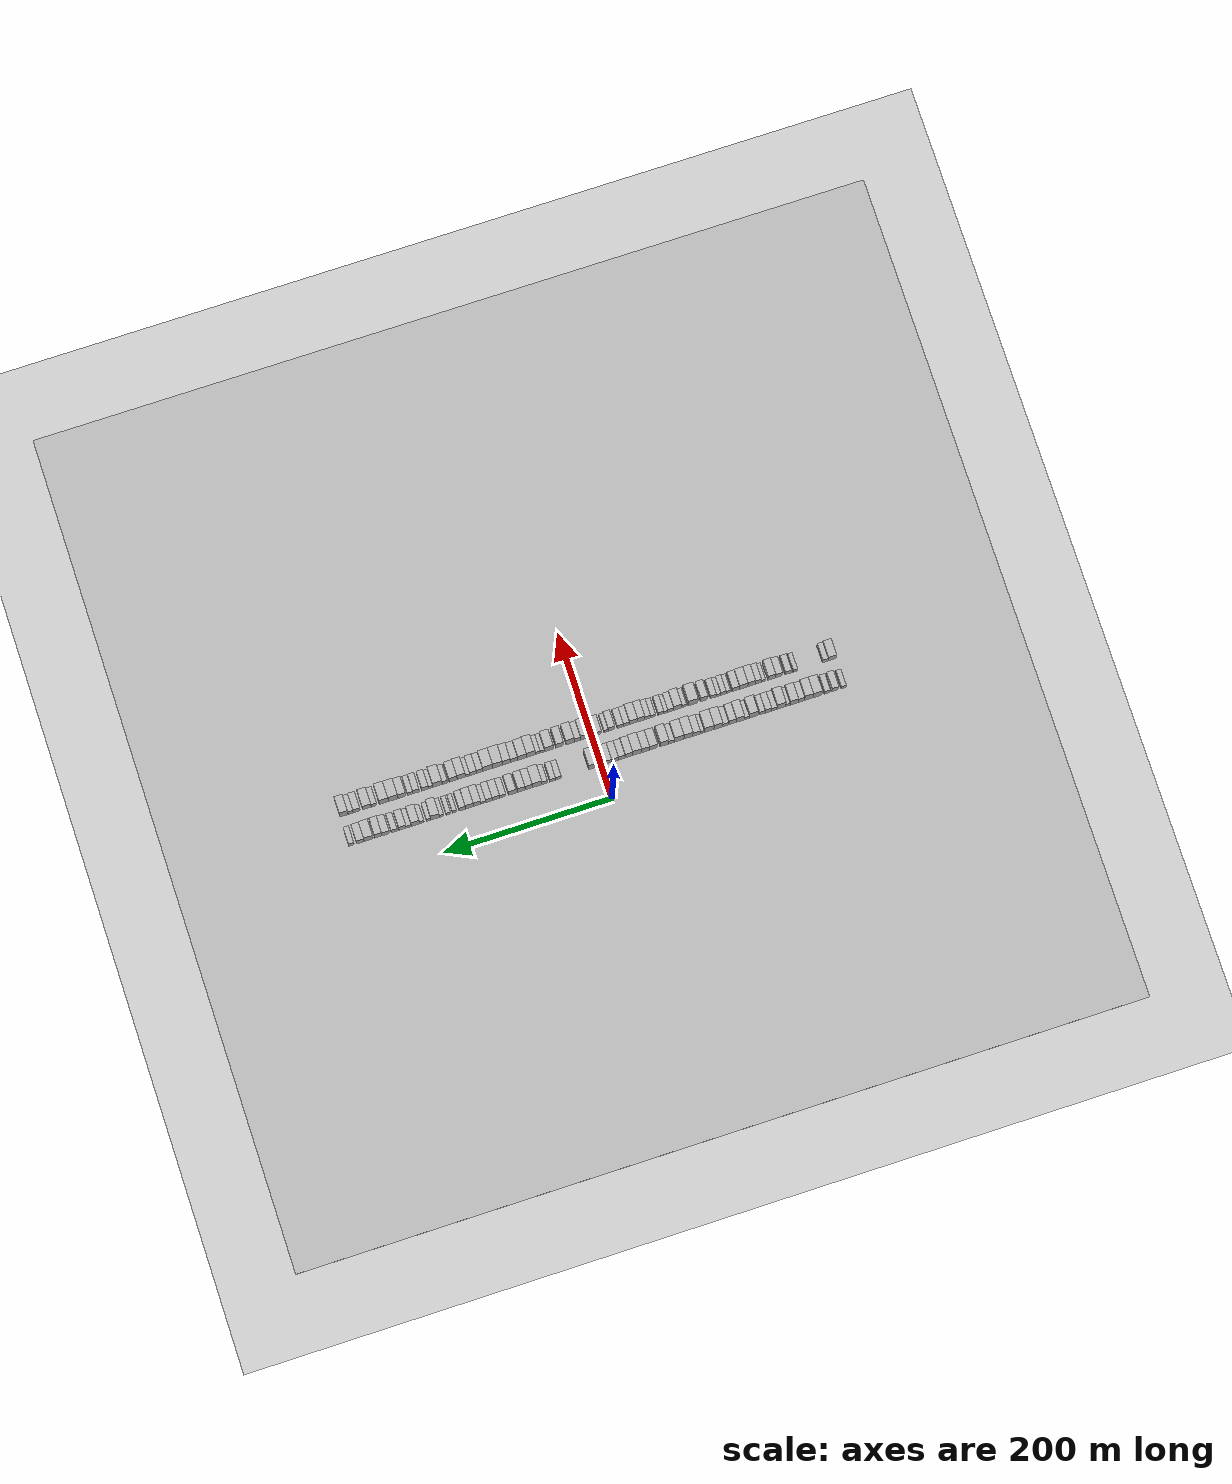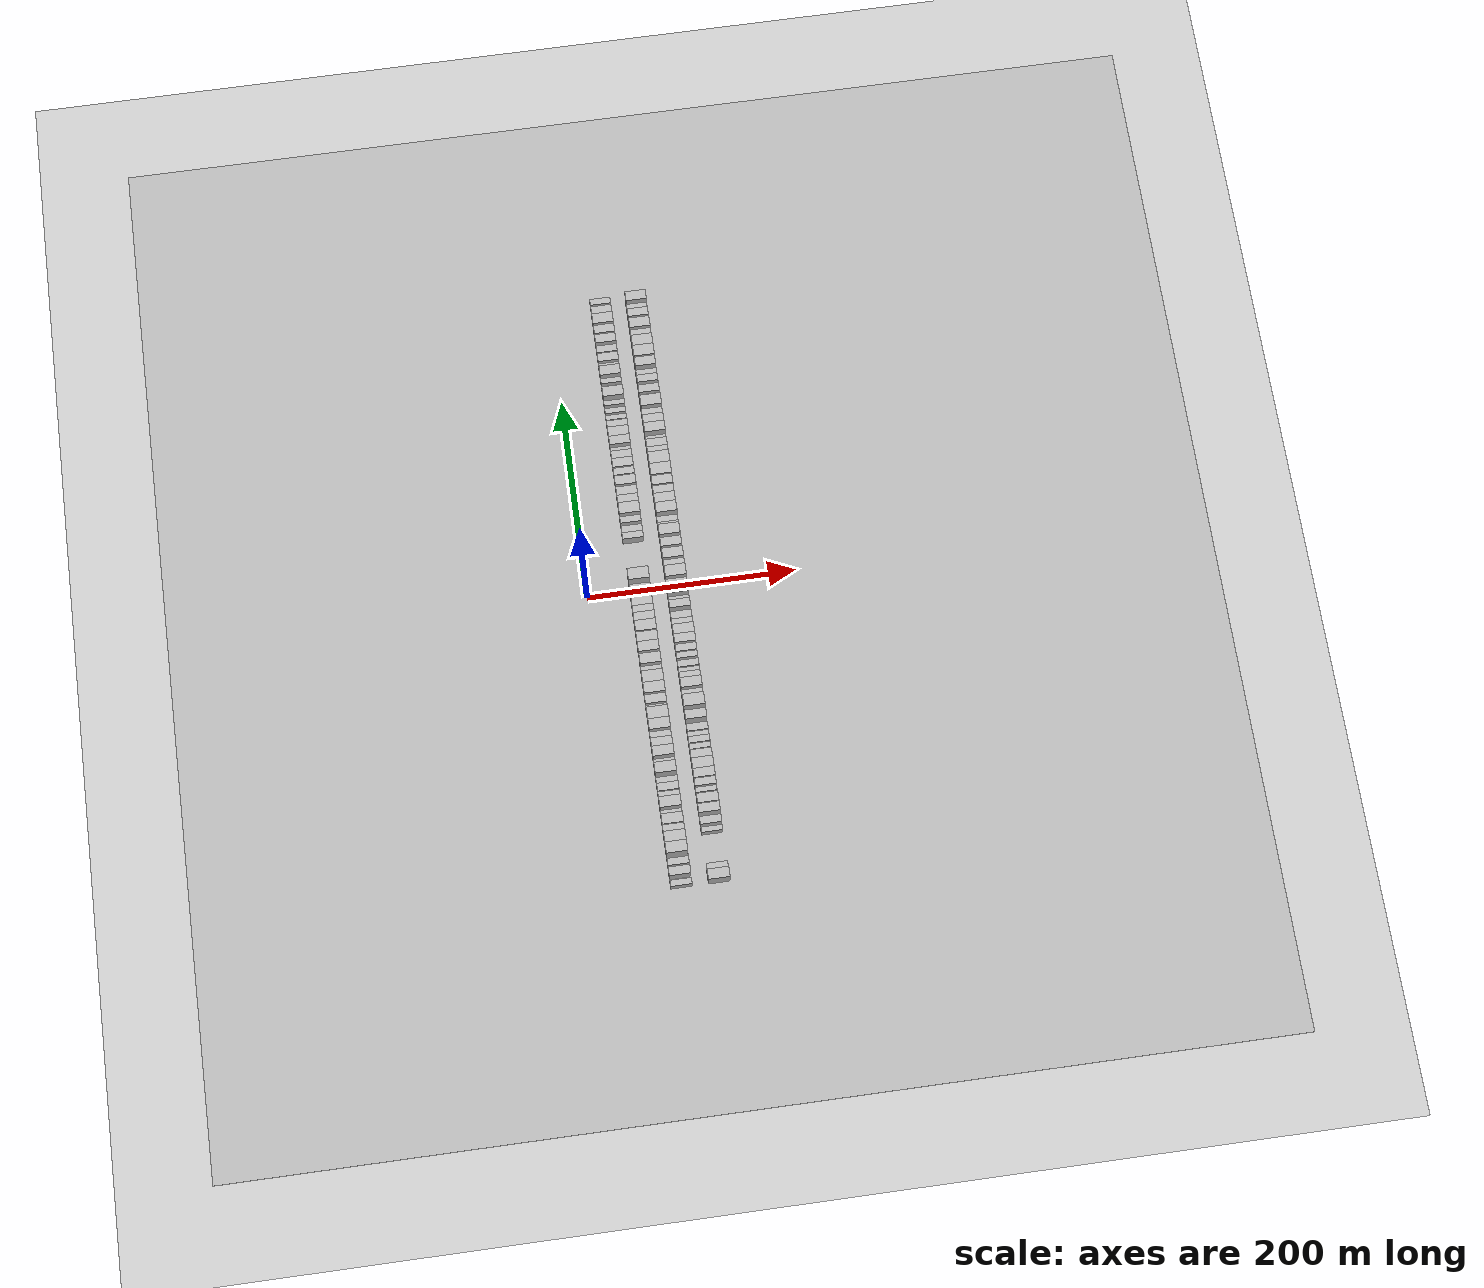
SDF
<?xml version="1.0" encoding="utf-8"?>

<sdf version="1.6">

   <world name="default">

      <gui fullscreen="0">

         <camera name="user_camera">

            <pose>-15 0 4.57585 0 0 0</pose>

            <view_controller>orbit</view_controller>

         </camera>

      </gui>

      <scene>

         <sky>

           <clouds>

             <speed>12</speed>

           </clouds>

         </sky>

         <ambient>0.4 0.4 0.4 1</ambient>

         <background>0.7 0.7 0.7 1</background>

         <shadows>1</shadows>

      </scene>

      <gravity>0 0 -9.8066</gravity>

      <magnetic_field>6e-06 2.3e-05 -4.2e-05</magnetic_field>

      <physics default="0" name="default_physics" type="ode">

         <ode>

            <solver>

               <type>quick</type>

               <iters>10</iters>

               <sor>1.0</sor>

               <use_dynamic_moi_rescaling>0</use_dynamic_moi_rescaling>

            </solver>

            <constraints>

               <cfm>0</cfm>

               <erp>0.2</erp>

               <contact_max_correcting_vel>100</contact_max_correcting_vel>

               <contact_surface_layer>0.001</contact_surface_layer>

            </constraints>

         </ode>

         <max_step_size>0.004</max_step_size>

         <real_time_factor>1</real_time_factor>

         <real_time_update_rate>250</real_time_update_rate>

      </physics>

      <light name="sun" type="directional">

         <cast_shadows>1</cast_shadows>

         <pose>0 0 10 0 0 0</pose>

         <diffuse>0.8 0.8 0.8 1</diffuse>

         <specular>0.2 0.2 0.2 1</specular>

         <attenuation>

            <range>1000</range>

            <constant>0.9</constant>

            <linear>0.01</linear>

            <quadratic>0.001</quadratic>

         </attenuation>

         <direction>-0.5 0.1 -0.9</direction>

      </light>

      <include>

         <name>ground_plane_1</name>

         <uri>model://HANNAS_ground_plane</uri>

         <pose>0 0 0  0 0 0</pose>

      </include>

      <include>

         <name>ground_plane_2</name>

         <uri>model://HANNAS_ground_plane</uri>

         <pose>100 0 0  0 0 0</pose>

      </include>

      <model name="building_1">

         <static>1</static>

         <pose frame="">50.0000 -287.0523 0 0.000000 0.000000 0.000000</pose>

         <link name="link">

            <pose frame="">0 0 6.00 0 0 0</pose>

            <collision name="collision">

               <geometry>

                  <box>

                     <size>20.0000 5.8953 12.0000</size>

                  </box>

               </geometry>

               <max_contacts>10</max_contacts>

               <surface>

                  <contact>

                     <ode/>

                  </contact>

                  <bounce/>

                  <friction>

                     <torsional>

                        <ode/>

                     </torsional>

                     <ode/>

                  </friction>

               </surface>

            </collision>

            <visual name="visual">

               <cast_shadows>0</cast_shadows>

               <geometry>

                  <box>

                     <size>20.0000 5.8953 12.0000</size>

                  </box>

               </geometry>

               <material>

                  <script>

                     <uri>model://HANNAS_wall/materials/scripts</uri>

                     <uri>model://HANNAS_wall/materials/textures</uri>

                     <name>vrc/HANNAS_wall</name>

                  </script>

               </material>

            </visual>

            <self_collide>0</self_collide>

            <enable_wind>0</enable_wind>

            <kinematic>0</kinematic>

         </link>

      </model>

      <model name="building_2">

         <static>1</static>

         <pose frame="">50.0000 -277.0093 0 0.000000 0.000000 0.000000</pose>

         <link name="link">

            <pose frame="">0 0 9.00 0 0 0</pose>

            <collision name="collision">

               <geometry>

                  <box>

                     <size>20.0000 8.1908 18.0000</size>

                  </box>

               </geometry>

               <max_contacts>10</max_contacts>

               <surface>

                  <contact>

                     <ode/>

                  </contact>

                  <bounce/>

                  <friction>

                     <torsional>

                        <ode/>

                     </torsional>

                     <ode/>

                  </friction>

               </surface>

            </collision>

            <visual name="visual">

               <cast_shadows>0</cast_shadows>

               <geometry>

                  <box>

                     <size>20.0000 8.1908 18.0000</size>

                  </box>

               </geometry>

               <material>

                  <script>

                     <uri>model://HANNAS_wall/materials/scripts</uri>

                     <uri>model://HANNAS_wall/materials/textures</uri>

                     <name>vrc/HANNAS_wall</name>

                  </script>

               </material>

            </visual>

            <self_collide>0</self_collide>

            <enable_wind>0</enable_wind>

            <kinematic>0</kinematic>

         </link>

      </model>

      <model name="building_3">

         <static>1</static>

         <pose frame="">50.0000 -267.5539 0 0.000000 0.000000 0.000000</pose>

         <link name="link">

            <pose frame="">0 0 7.50 0 0 0</pose>

            <collision name="collision">

               <geometry>

                  <box>

                     <size>20.0000 6.7200 15.0000</size>

                  </box>

               </geometry>

               <max_contacts>10</max_contacts>

               <surface>

                  <contact>

                     <ode/>

                  </contact>

                  <bounce/>

                  <friction>

                     <torsional>

                        <ode/>

                     </torsional>

                     <ode/>

                  </friction>

               </surface>

            </collision>

            <visual name="visual">

               <cast_shadows>0</cast_shadows>

               <geometry>

                  <box>

                     <size>20.0000 6.7200 15.0000</size>

                  </box>

               </geometry>

               <material>

                  <script>

                     <uri>model://HANNAS_wall/materials/scripts</uri>

                     <uri>model://HANNAS_wall/materials/textures</uri>

                     <name>vrc/HANNAS_wall</name>

                  </script>

               </material>

            </visual>

            <self_collide>0</self_collide>

            <enable_wind>0</enable_wind>

            <kinematic>0</kinematic>

         </link>

      </model>

      <model name="building_4">

         <static>1</static>

         <pose frame="">50.0000 -255.9234 0 0.000000 0.000000 0.000000</pose>

         <link name="link">

            <pose frame="">0 0 12.00 0 0 0</pose>

            <collision name="collision">

               <geometry>

                  <box>

                     <size>20.0000 10.5409 24.0000</size>

                  </box>

               </geometry>

               <max_contacts>10</max_contacts>

               <surface>

                  <contact>

                     <ode/>

                  </contact>

                  <bounce/>

                  <friction>

                     <torsional>

                        <ode/>

                     </torsional>

                     <ode/>

                  </friction>

               </surface>

            </collision>

            <visual name="visual">

               <cast_shadows>0</cast_shadows>

               <geometry>

                  <box>

                     <size>20.0000 10.5409 24.0000</size>

                  </box>

               </geometry>

               <material>

                  <script>

                     <uri>model://HANNAS_wall/materials/scripts</uri>

                     <uri>model://HANNAS_wall/materials/textures</uri>

                     <name>vrc/HANNAS_wall</name>

                  </script>

               </material>

            </visual>

            <self_collide>0</self_collide>

            <enable_wind>0</enable_wind>

            <kinematic>0</kinematic>

         </link>

      </model>

      <model name="building_5">

         <static>1</static>

         <pose frame="">50.0000 -245.6184 0 0.000000 0.000000 0.000000</pose>

         <link name="link">

            <pose frame="">0 0 12.00 0 0 0</pose>

            <collision name="collision">

               <geometry>

                  <box>

                     <size>20.0000 10.0692 24.0000</size>

                  </box>

               </geometry>

               <max_contacts>10</max_contacts>

               <surface>

                  <contact>

                     <ode/>

                  </contact>

                  <bounce/>

                  <friction>

                     <torsional>

                        <ode/>

                     </torsional>

                     <ode/>

                  </friction>

               </surface>

            </collision>

            <visual name="visual">

               <cast_shadows>0</cast_shadows>

               <geometry>

                  <box>

                     <size>20.0000 10.0692 24.0000</size>

                  </box>

               </geometry>

               <material>

                  <script>

                     <uri>model://HANNAS_wall/materials/scripts</uri>

                     <uri>model://HANNAS_wall/materials/textures</uri>

                     <name>vrc/HANNAS_wall</name>

                  </script>

               </material>

            </visual>

            <self_collide>0</self_collide>

            <enable_wind>0</enable_wind>

            <kinematic>0</kinematic>

         </link>

      </model>

      <model name="building_6">

         <static>1</static>

         <pose frame="">50.0000 -236.8694 0 0.000000 0.000000 0.000000</pose>

         <link name="link">

            <pose frame="">0 0 9.00 0 0 0</pose>

            <collision name="collision">

               <geometry>

                  <box>

                     <size>20.0000 7.4288 18.0000</size>

                  </box>

               </geometry>

               <max_contacts>10</max_contacts>

               <surface>

                  <contact>

                     <ode/>

                  </contact>

                  <bounce/>

                  <friction>

                     <torsional>

                        <ode/>

                     </torsional>

                     <ode/>

                  </friction>

               </surface>

            </collision>

            <visual name="visual">

               <cast_shadows>0</cast_shadows>

               <geometry>

                  <box>

                     <size>20.0000 7.4288 18.0000</size>

                  </box>

               </geometry>

               <material>

                  <script>

                     <uri>model://HANNAS_wall/materials/scripts</uri>

                     <uri>model://HANNAS_wall/materials/textures</uri>

                     <name>vrc/HANNAS_wall</name>

                  </script>

               </material>

            </visual>

            <self_collide>0</self_collide>

            <enable_wind>0</enable_wind>

            <kinematic>0</kinematic>

         </link>

      </model>

      <model name="building_7">

         <static>1</static>

         <pose frame="">50.0000 -228.2366 0 0.000000 0.000000 0.000000</pose>

         <link name="link">

            <pose frame="">0 0 10.50 0 0 0</pose>

            <collision name="collision">

               <geometry>

                  <box>

                     <size>20.0000 9.8366 21.0000</size>

                  </box>

               </geometry>

               <max_contacts>10</max_contacts>

               <surface>

                  <contact>

                     <ode/>

                  </contact>

                  <bounce/>

                  <friction>

                     <torsional>

                        <ode/>

                     </torsional>

                     <ode/>

                  </friction>

               </surface>

            </collision>

            <visual name="visual">

               <cast_shadows>0</cast_shadows>

               <geometry>

                  <box>

                     <size>20.0000 9.8366 21.0000</size>

                  </box>

               </geometry>

               <material>

                  <script>

                     <uri>model://HANNAS_wall/materials/scripts</uri>

                     <uri>model://HANNAS_wall/materials/textures</uri>

                     <name>vrc/HANNAS_wall</name>

                  </script>

               </material>

            </visual>

            <self_collide>0</self_collide>

            <enable_wind>0</enable_wind>

            <kinematic>0</kinematic>

         </link>

      </model>

      <model name="building_8">

         <static>1</static>

         <pose frame="">50.0000 -220.6648 0 0.000000 0.000000 0.000000</pose>

         <link name="link">

            <pose frame="">0 0 6.00 0 0 0</pose>

            <collision name="collision">

               <geometry>

                  <box>

                     <size>20.0000 5.3072 12.0000</size>

                  </box>

               </geometry>

               <max_contacts>10</max_contacts>

               <surface>

                  <contact>

                     <ode/>

                  </contact>

                  <bounce/>

                  <friction>

                     <torsional>

                        <ode/>

                     </torsional>

                     <ode/>

                  </friction>

               </surface>

            </collision>

            <visual name="visual">

               <cast_shadows>0</cast_shadows>

               <geometry>

                  <box>

                     <size>20.0000 5.3072 12.0000</size>

                  </box>

               </geometry>

               <material>

                  <script>

                     <uri>model://HANNAS_wall/materials/scripts</uri>

                     <uri>model://HANNAS_wall/materials/textures</uri>

                     <name>vrc/HANNAS_wall</name>

                  </script>

               </material>

            </visual>

            <self_collide>0</self_collide>

            <enable_wind>0</enable_wind>

            <kinematic>0</kinematic>

         </link>

      </model>

      <model name="building_9">

         <static>1</static>

         <pose frame="">50.0000 -212.8576 0 0.000000 0.000000 0.000000</pose>

         <link name="link">

            <pose frame="">0 0 12.00 0 0 0</pose>

            <collision name="collision">

               <geometry>

                  <box>

                     <size>20.0000 10.3071 24.0000</size>

                  </box>

               </geometry>

               <max_contacts>10</max_contacts>

               <surface>

                  <contact>

                     <ode/>

                  </contact>

                  <bounce/>

                  <friction>

                     <torsional>

                        <ode/>

                     </torsional>

                     <ode/>

                  </friction>

               </surface>

            </collision>

            <visual name="visual">

               <cast_shadows>0</cast_shadows>

               <geometry>

                  <box>

                     <size>20.0000 10.3071 24.0000</size>

                  </box>

               </geometry>

               <material>

                  <script>

                     <uri>model://HANNAS_wall/materials/scripts</uri>

                     <uri>model://HANNAS_wall/materials/textures</uri>

                     <name>vrc/HANNAS_wall</name>

                  </script>

               </material>

            </visual>

            <self_collide>0</self_collide>

            <enable_wind>0</enable_wind>

            <kinematic>0</kinematic>

         </link>

      </model>

      <model name="building_10">

         <static>1</static>

         <pose frame="">50.0000 -204.3506 0 0.000000 0.000000 0.000000</pose>

         <link name="link">

            <pose frame="">0 0 7.50 0 0 0</pose>

            <collision name="collision">

               <geometry>

                  <box>

                     <size>20.0000 6.7071 15.0000</size>

                  </box>

               </geometry>

               <max_contacts>10</max_contacts>

               <surface>

                  <contact>

                     <ode/>

                  </contact>

                  <bounce/>

                  <friction>

                     <torsional>

                        <ode/>

                     </torsional>

                     <ode/>

                  </friction>

               </surface>

            </collision>

            <visual name="visual">

               <cast_shadows>0</cast_shadows>

               <geometry>

                  <box>

                     <size>20.0000 6.7071 15.0000</size>

                  </box>

               </geometry>

               <material>

                  <script>

                     <uri>model://HANNAS_wall/materials/scripts</uri>

                     <uri>model://HANNAS_wall/materials/textures</uri>

                     <name>vrc/HANNAS_wall</name>

                  </script>

               </material>

            </visual>

            <self_collide>0</self_collide>

            <enable_wind>0</enable_wind>

            <kinematic>0</kinematic>

         </link>

      </model>

      <model name="building_11">

         <static>1</static>

         <pose frame="">50.0000 -197.2316 0 0.000000 0.000000 0.000000</pose>

         <link name="link">

            <pose frame="">0 0 9.00 0 0 0</pose>

            <collision name="collision">

               <geometry>

                  <box>

                     <size>20.0000 7.5308 18.0000</size>

                  </box>

               </geometry>

               <max_contacts>10</max_contacts>

               <surface>

                  <contact>

                     <ode/>

                  </contact>

                  <bounce/>

                  <friction>

                     <torsional>

                        <ode/>

                     </torsional>

                     <ode/>

                  </friction>

               </surface>

            </collision>

            <visual name="visual">

               <cast_shadows>0</cast_shadows>

               <geometry>

                  <box>

                     <size>20.0000 7.5308 18.0000</size>

                  </box>

               </geometry>

               <material>

                  <script>

                     <uri>model://HANNAS_wall/materials/scripts</uri>

                     <uri>model://HANNAS_wall/materials/textures</uri>

                     <name>vrc/HANNAS_wall</name>

                  </script>

               </material>

            </visual>

            <self_collide>0</self_collide>

            <enable_wind>0</enable_wind>

            <kinematic>0</kinematic>

         </link>

      </model>

      <model name="building_12">

         <static>1</static>

         <pose frame="">50.0000 -190.2864 0 0.000000 0.000000 0.000000</pose>

         <link name="link">

            <pose frame="">0 0 7.50 0 0 0</pose>

            <collision name="collision">

               <geometry>

                  <box>

                     <size>20.0000 6.3596 15.0000</size>

                  </box>

               </geometry>

               <max_contacts>10</max_contacts>

               <surface>

                  <contact>

                     <ode/>

                  </contact>

                  <bounce/>

                  <friction>

                     <torsional>

                        <ode/>

                     </torsional>

                     <ode/>

                  </friction>

               </surface>

            </collision>

            <visual name="visual">

               <cast_shadows>0</cast_shadows>

               <geometry>

                  <box>

                     <size>20.0000 6.3596 15.0000</size>

                  </box>

               </geometry>

               <material>

                  <script>

                     <uri>model://HANNAS_wall/materials/scripts</uri>

                     <uri>model://HANNAS_wall/materials/textures</uri>

                     <name>vrc/HANNAS_wall</name>

                  </script>

               </material>

            </visual>

            <self_collide>0</self_collide>

            <enable_wind>0</enable_wind>

            <kinematic>0</kinematic>

         </link>

      </model>

      <model name="building_13">

         <static>1</static>

         <pose frame="">50.0000 -179.9060 0 0.000000 0.000000 0.000000</pose>

         <link name="link">

            <pose frame="">0 0 12.00 0 0 0</pose>

            <collision name="collision">

               <geometry>

                  <box>

                     <size>20.0000 10.4011 24.0000</size>

                  </box>

               </geometry>

               <max_contacts>10</max_contacts>

               <surface>

                  <contact>

                     <ode/>

                  </contact>

                  <bounce/>

                  <friction>

                     <torsional>

                        <ode/>

                     </torsional>

                     <ode/>

                  </friction>

               </surface>

            </collision>

            <visual name="visual">

               <cast_shadows>0</cast_shadows>

               <geometry>

                  <box>

                     <size>20.0000 10.4011 24.0000</size>

                  </box>

               </geometry>

               <material>

                  <script>

                     <uri>model://HANNAS_wall/materials/scripts</uri>

                     <uri>model://HANNAS_wall/materials/textures</uri>

                     <name>vrc/HANNAS_wall</name>

                  </script>

               </material>

            </visual>

            <self_collide>0</self_collide>

            <enable_wind>0</enable_wind>

            <kinematic>0</kinematic>

         </link>

      </model>

      <model name="building_14">

         <static>1</static>

         <pose frame="">50.0000 -171.7986 0 0.000000 0.000000 0.000000</pose>

         <link name="link">

            <pose frame="">0 0 6.00 0 0 0</pose>

            <collision name="collision">

               <geometry>

                  <box>

                     <size>20.0000 5.8136 12.0000</size>

                  </box>

               </geometry>

               <max_contacts>10</max_contacts>

               <surface>

                  <contact>

                     <ode/>

                  </contact>

                  <bounce/>

                  <friction>

                     <torsional>

                        <ode/>

                     </torsional>

                     <ode/>

                  </friction>

               </surface>

            </collision>

            <visual name="visual">

               <cast_shadows>0</cast_shadows>

               <geometry>

                  <box>

                     <size>20.0000 5.8136 12.0000</size>

                  </box>

               </geometry>

               <material>

                  <script>

                     <uri>model://HANNAS_wall/materials/scripts</uri>

                     <uri>model://HANNAS_wall/materials/textures</uri>

                     <name>vrc/HANNAS_wall</name>

                  </script>

               </material>

            </visual>

            <self_collide>0</self_collide>

            <enable_wind>0</enable_wind>

            <kinematic>0</kinematic>

         </link>

      </model>

      <model name="building_15">

         <static>1</static>

         <pose frame="">50.0000 -164.0420 0 0.000000 0.000000 0.000000</pose>

         <link name="link">

            <pose frame="">0 0 12.00 0 0 0</pose>

            <collision name="collision">

               <geometry>

                  <box>

                     <size>20.0000 9.6997 24.0000</size>

                  </box>

               </geometry>

               <max_contacts>10</max_contacts>

               <surface>

                  <contact>

                     <ode/>

                  </contact>

                  <bounce/>

                  <friction>

                     <torsional>

                        <ode/>

                     </torsional>

                     <ode/>

                  </friction>

               </surface>

            </collision>

            <visual name="visual">

               <cast_shadows>0</cast_shadows>

               <geometry>

                  <box>

                     <size>20.0000 9.6997 24.0000</size>

                  </box>

               </geometry>

               <material>

                  <script>

                     <uri>model://HANNAS_wall/materials/scripts</uri>

                     <uri>model://HANNAS_wall/materials/textures</uri>

                     <name>vrc/HANNAS_wall</name>

                  </script>

               </material>

            </visual>

            <self_collide>0</self_collide>

            <enable_wind>0</enable_wind>

            <kinematic>0</kinematic>

         </link>

      </model>

      <model name="building_16">

         <static>1</static>

         <pose frame="">50.0000 -154.8154 0 0.000000 0.000000 0.000000</pose>

         <link name="link">

            <pose frame="">0 0 10.50 0 0 0</pose>

            <collision name="collision">

               <geometry>

                  <box>

                     <size>20.0000 8.7535 21.0000</size>

                  </box>

               </geometry>

               <max_contacts>10</max_contacts>

               <surface>

                  <contact>

                     <ode/>

                  </contact>

                  <bounce/>

                  <friction>

                     <torsional>

                        <ode/>

                     </torsional>

                     <ode/>

                  </friction>

               </surface>

            </collision>

            <visual name="visual">

               <cast_shadows>0</cast_shadows>

               <geometry>

                  <box>

                     <size>20.0000 8.7535 21.0000</size>

                  </box>

               </geometry>

               <material>

                  <script>

                     <uri>model://HANNAS_wall/materials/scripts</uri>

                     <uri>model://HANNAS_wall/materials/textures</uri>

                     <name>vrc/HANNAS_wall</name>

                  </script>

               </material>

            </visual>

            <self_collide>0</self_collide>

            <enable_wind>0</enable_wind>

            <kinematic>0</kinematic>

         </link>

      </model>

      <model name="building_17">

         <static>1</static>

         <pose frame="">50.0000 -146.7566 0 0.000000 0.000000 0.000000</pose>

         <link name="link">

            <pose frame="">0 0 7.50 0 0 0</pose>

            <collision name="collision">

               <geometry>

                  <box>

                     <size>20.0000 7.3642 15.0000</size>

                  </box>

               </geometry>

               <max_contacts>10</max_contacts>

               <surface>

                  <contact>

                     <ode/>

                  </contact>

                  <bounce/>

                  <friction>

                     <torsional>

                        <ode/>

                     </torsional>

                     <ode/>

                  </friction>

               </surface>

            </collision>

            <visual name="visual">

               <cast_shadows>0</cast_shadows>

               <geometry>

                  <box>

                     <size>20.0000 7.3642 15.0000</size>

                  </box>

               </geometry>

               <material>

                  <script>

                     <uri>model://HANNAS_wall/materials/scripts</uri>

                     <uri>model://HANNAS_wall/materials/textures</uri>

                     <name>vrc/HANNAS_wall</name>

                  </script>

               </material>

            </visual>

            <self_collide>0</self_collide>

            <enable_wind>0</enable_wind>

            <kinematic>0</kinematic>

         </link>

      </model>

      <model name="building_18">

         <static>1</static>

         <pose frame="">50.0000 -137.8988 0 0.000000 0.000000 0.000000</pose>

         <link name="link">

            <pose frame="">0 0 12.00 0 0 0</pose>

            <collision name="collision">

               <geometry>

                  <box>

                     <size>20.0000 10.3513 24.0000</size>

                  </box>

               </geometry>

               <max_contacts>10</max_contacts>

               <surface>

                  <contact>

                     <ode/>

                  </contact>

                  <bounce/>

                  <friction>

                     <torsional>

                        <ode/>

                     </torsional>

                     <ode/>

                  </friction>

               </surface>

            </collision>

            <visual name="visual">

               <cast_shadows>0</cast_shadows>

               <geometry>

                  <box>

                     <size>20.0000 10.3513 24.0000</size>

                  </box>

               </geometry>

               <material>

                  <script>

                     <uri>model://HANNAS_wall/materials/scripts</uri>

                     <uri>model://HANNAS_wall/materials/textures</uri>

                     <name>vrc/HANNAS_wall</name>

                  </script>

               </material>

            </visual>

            <self_collide>0</self_collide>

            <enable_wind>0</enable_wind>

            <kinematic>0</kinematic>

         </link>

      </model>

      <model name="building_19">

         <static>1</static>

         <pose frame="">50.0000 -127.0697 0 0.000000 0.000000 0.000000</pose>

         <link name="link">

            <pose frame="">0 0 12.00 0 0 0</pose>

            <collision name="collision">

               <geometry>

                  <box>

                     <size>20.0000 11.3070 24.0000</size>

                  </box>

               </geometry>

               <max_contacts>10</max_contacts>

               <surface>

                  <contact>

                     <ode/>

                  </contact>

                  <bounce/>

                  <friction>

                     <torsional>

                        <ode/>

                     </torsional>

                     <ode/>

                  </friction>

               </surface>

            </collision>

            <visual name="visual">

               <cast_shadows>0</cast_shadows>

               <geometry>

                  <box>

                     <size>20.0000 11.3070 24.0000</size>

                  </box>

               </geometry>

               <material>

                  <script>

                     <uri>model://HANNAS_wall/materials/scripts</uri>

                     <uri>model://HANNAS_wall/materials/textures</uri>

                     <name>vrc/HANNAS_wall</name>

                  </script>

               </material>

            </visual>

            <self_collide>0</self_collide>

            <enable_wind>0</enable_wind>

            <kinematic>0</kinematic>

         </link>

      </model>

      <model name="building_20">

         <static>1</static>

         <pose frame="">50.0000 -118.8807 0 0.000000 0.000000 0.000000</pose>

         <link name="link">

            <pose frame="">0 0 6.00 0 0 0</pose>

            <collision name="collision">

               <geometry>

                  <box>

                     <size>20.0000 5.0709 12.0000</size>

                  </box>

               </geometry>

               <max_contacts>10</max_contacts>

               <surface>

                  <contact>

                     <ode/>

                  </contact>

                  <bounce/>

                  <friction>

                     <torsional>

                        <ode/>

                     </torsional>

                     <ode/>

                  </friction>

               </surface>

            </collision>

            <visual name="visual">

               <cast_shadows>0</cast_shadows>

               <geometry>

                  <box>

                     <size>20.0000 5.0709 12.0000</size>

                  </box>

               </geometry>

               <material>

                  <script>

                     <uri>model://HANNAS_wall/materials/scripts</uri>

                     <uri>model://HANNAS_wall/materials/textures</uri>

                     <name>vrc/HANNAS_wall</name>

                  </script>

               </material>

            </visual>

            <self_collide>0</self_collide>

            <enable_wind>0</enable_wind>

            <kinematic>0</kinematic>

         </link>

      </model>

      <model name="building_21">

         <static>1</static>

         <pose frame="">50.0000 -112.0234 0 0.000000 0.000000 0.000000</pose>

         <link name="link">

            <pose frame="">0 0 9.00 0 0 0</pose>

            <collision name="collision">

               <geometry>

                  <box>

                     <size>20.0000 8.6437 18.0000</size>

                  </box>

               </geometry>

               <max_contacts>10</max_contacts>

               <surface>

                  <contact>

                     <ode/>

                  </contact>

                  <bounce/>

                  <friction>

                     <torsional>

                        <ode/>

                     </torsional>

                     <ode/>

                  </friction>

               </surface>

            </collision>

            <visual name="visual">

               <cast_shadows>0</cast_shadows>

               <geometry>

                  <box>

                     <size>20.0000 8.6437 18.0000</size>

                  </box>

               </geometry>

               <material>

                  <script>

                     <uri>model://HANNAS_wall/materials/scripts</uri>

                     <uri>model://HANNAS_wall/materials/textures</uri>

                     <name>vrc/HANNAS_wall</name>

                  </script>

               </material>

            </visual>

            <self_collide>0</self_collide>

            <enable_wind>0</enable_wind>

            <kinematic>0</kinematic>

         </link>

      </model>

      <model name="building_22">

         <static>1</static>

         <pose frame="">50.0000 -102.4219 0 0.000000 0.000000 0.000000</pose>

         <link name="link">

            <pose frame="">0 0 12.00 0 0 0</pose>

            <collision name="collision">

               <geometry>

                  <box>

                     <size>20.0000 10.5594 24.0000</size>

                  </box>

               </geometry>

               <max_contacts>10</max_contacts>

               <surface>

                  <contact>

                     <ode/>

                  </contact>

                  <bounce/>

                  <friction>

                     <torsional>

                        <ode/>

                     </torsional>

                     <ode/>

                  </friction>

               </surface>

            </collision>

            <visual name="visual">

               <cast_shadows>0</cast_shadows>

               <geometry>

                  <box>

                     <size>20.0000 10.5594 24.0000</size>

                  </box>

               </geometry>

               <material>

                  <script>

                     <uri>model://HANNAS_wall/materials/scripts</uri>

                     <uri>model://HANNAS_wall/materials/textures</uri>

                     <name>vrc/HANNAS_wall</name>

                  </script>

               </material>

            </visual>

            <self_collide>0</self_collide>

            <enable_wind>0</enable_wind>

            <kinematic>0</kinematic>

         </link>

      </model>

      <model name="building_23">

         <static>1</static>

         <pose frame="">50.0000 -91.5550 0 0.000000 0.000000 0.000000</pose>

         <link name="link">

            <pose frame="">0 0 12.00 0 0 0</pose>

            <collision name="collision">

               <geometry>

                  <box>

                     <size>20.0000 11.1743 24.0000</size>

                  </box>

               </geometry>

               <max_contacts>10</max_contacts>

               <surface>

                  <contact>

                     <ode/>

                  </contact>

                  <bounce/>

                  <friction>

                     <torsional>

                        <ode/>

                     </torsional>

                     <ode/>

                  </friction>

               </surface>

            </collision>

            <visual name="visual">

               <cast_shadows>0</cast_shadows>

               <geometry>

                  <box>

                     <size>20.0000 11.1743 24.0000</size>

                  </box>

               </geometry>

               <material>

                  <script>

                     <uri>model://HANNAS_wall/materials/scripts</uri>

                     <uri>model://HANNAS_wall/materials/textures</uri>

                     <name>vrc/HANNAS_wall</name>

                  </script>

               </material>

            </visual>

            <self_collide>0</self_collide>

            <enable_wind>0</enable_wind>

            <kinematic>0</kinematic>

         </link>

      </model>

      <model name="building_24">

         <static>1</static>

         <pose frame="">50.0000 -82.5358 0 0.000000 0.000000 0.000000</pose>

         <link name="link">

            <pose frame="">0 0 7.50 0 0 0</pose>

            <collision name="collision">

               <geometry>

                  <box>

                     <size>20.0000 6.8641 15.0000</size>

                  </box>

               </geometry>

               <max_contacts>10</max_contacts>

               <surface>

                  <contact>

                     <ode/>

                  </contact>

                  <bounce/>

                  <friction>

                     <torsional>

                        <ode/>

                     </torsional>

                     <ode/>

                  </friction>

               </surface>

            </collision>

            <visual name="visual">

               <cast_shadows>0</cast_shadows>

               <geometry>

                  <box>

                     <size>20.0000 6.8641 15.0000</size>

                  </box>

               </geometry>

               <material>

                  <script>

                     <uri>model://HANNAS_wall/materials/scripts</uri>

                     <uri>model://HANNAS_wall/materials/textures</uri>

                     <name>vrc/HANNAS_wall</name>

                  </script>

               </material>

            </visual>

            <self_collide>0</self_collide>

            <enable_wind>0</enable_wind>

            <kinematic>0</kinematic>

         </link>

      </model>

      <model name="building_25">

         <static>1</static>

         <pose frame="">50.0000 -74.0239 0 0.000000 0.000000 0.000000</pose>

         <link name="link">

            <pose frame="">0 0 12.00 0 0 0</pose>

            <collision name="collision">

               <geometry>

                  <box>

                     <size>20.0000 10.1597 24.0000</size>

                  </box>

               </geometry>

               <max_contacts>10</max_contacts>

               <surface>

                  <contact>

                     <ode/>

                  </contact>

                  <bounce/>

                  <friction>

                     <torsional>

                        <ode/>

                     </torsional>

                     <ode/>

                  </friction>

               </surface>

            </collision>

            <visual name="visual">

               <cast_shadows>0</cast_shadows>

               <geometry>

                  <box>

                     <size>20.0000 10.1597 24.0000</size>

                  </box>

               </geometry>

               <material>

                  <script>

                     <uri>model://HANNAS_wall/materials/scripts</uri>

                     <uri>model://HANNAS_wall/materials/textures</uri>

                     <name>vrc/HANNAS_wall</name>

                  </script>

               </material>

            </visual>

            <self_collide>0</self_collide>

            <enable_wind>0</enable_wind>

            <kinematic>0</kinematic>

         </link>

      </model>

      <model name="building_26">

         <static>1</static>

         <pose frame="">50.0000 -61.0833 0 0.000000 0.000000 0.000000</pose>

         <link name="link">

            <pose frame="">0 0 10.50 0 0 0</pose>

            <collision name="collision">

               <geometry>

                  <box>

                     <size>20.0000 9.7216 21.0000</size>

                  </box>

               </geometry>

               <max_contacts>10</max_contacts>

               <surface>

                  <contact>

                     <ode/>

                  </contact>

                  <bounce/>

                  <friction>

                     <torsional>

                        <ode/>

                     </torsional>

                     <ode/>

                  </friction>

               </surface>

            </collision>

            <visual name="visual">

               <cast_shadows>0</cast_shadows>

               <geometry>

                  <box>

                     <size>20.0000 9.7216 21.0000</size>

                  </box>

               </geometry>

               <material>

                  <script>

                     <uri>model://HANNAS_wall/materials/scripts</uri>

                     <uri>model://HANNAS_wall/materials/textures</uri>

                     <name>vrc/HANNAS_wall</name>

                  </script>

               </material>

            </visual>

            <self_collide>0</self_collide>

            <enable_wind>0</enable_wind>

            <kinematic>0</kinematic>

         </link>

      </model>

      <model name="building_27">

         <static>1</static>

         <pose frame="">50.0000 -51.4662 0 0.000000 0.000000 0.000000</pose>

         <link name="link">

            <pose frame="">0 0 10.50 0 0 0</pose>

            <collision name="collision">

               <geometry>

                  <box>

                     <size>20.0000 9.5127 21.0000</size>

                  </box>

               </geometry>

               <max_contacts>10</max_contacts>

               <surface>

                  <contact>

                     <ode/>

                  </contact>

                  <bounce/>

                  <friction>

                     <torsional>

                        <ode/>

                     </torsional>

                     <ode/>

                  </friction>

               </surface>

            </collision>

            <visual name="visual">

               <cast_shadows>0</cast_shadows>

               <geometry>

                  <box>

                     <size>20.0000 9.5127 21.0000</size>

                  </box>

               </geometry>

               <material>

                  <script>

                     <uri>model://HANNAS_wall/materials/scripts</uri>

                     <uri>model://HANNAS_wall/materials/textures</uri>

                     <name>vrc/HANNAS_wall</name>

                  </script>

               </material>

            </visual>

            <self_collide>0</self_collide>

            <enable_wind>0</enable_wind>

            <kinematic>0</kinematic>

         </link>

      </model>

      <model name="building_28">

         <static>1</static>

         <pose frame="">50.0000 -41.4690 0 0.000000 0.000000 0.000000</pose>

         <link name="link">

            <pose frame="">0 0 12.00 0 0 0</pose>

            <collision name="collision">

               <geometry>

                  <box>

                     <size>20.0000 10.4816 24.0000</size>

                  </box>

               </geometry>

               <max_contacts>10</max_contacts>

               <surface>

                  <contact>

                     <ode/>

                  </contact>

                  <bounce/>

                  <friction>

                     <torsional>

                        <ode/>

                     </torsional>

                     <ode/>

                  </friction>

               </surface>

            </collision>

            <visual name="visual">

               <cast_shadows>0</cast_shadows>

               <geometry>

                  <box>

                     <size>20.0000 10.4816 24.0000</size>

                  </box>

               </geometry>

               <material>

                  <script>

                     <uri>model://HANNAS_wall/materials/scripts</uri>

                     <uri>model://HANNAS_wall/materials/textures</uri>

                     <name>vrc/HANNAS_wall</name>

                  </script>

               </material>

            </visual>

            <self_collide>0</self_collide>

            <enable_wind>0</enable_wind>

            <kinematic>0</kinematic>

         </link>

      </model>

      <model name="building_29">

         <static>1</static>

         <pose frame="">50.0000 -31.7760 0 0.000000 0.000000 0.000000</pose>

         <link name="link">

            <pose frame="">0 0 10.50 0 0 0</pose>

            <collision name="collision">

               <geometry>

                  <box>

                     <size>20.0000 8.9044 21.0000</size>

                  </box>

               </geometry>

               <max_contacts>10</max_contacts>

               <surface>

                  <contact>

                     <ode/>

                  </contact>

                  <bounce/>

                  <friction>

                     <torsional>

                        <ode/>

                     </torsional>

                     <ode/>

                  </friction>

               </surface>

            </collision>

            <visual name="visual">

               <cast_shadows>0</cast_shadows>

               <geometry>

                  <box>

                     <size>20.0000 8.9044 21.0000</size>

                  </box>

               </geometry>

               <material>

                  <script>

                     <uri>model://HANNAS_wall/materials/scripts</uri>

                     <uri>model://HANNAS_wall/materials/textures</uri>

                     <name>vrc/HANNAS_wall</name>

                  </script>

               </material>

            </visual>

            <self_collide>0</self_collide>

            <enable_wind>0</enable_wind>

            <kinematic>0</kinematic>

         </link>

      </model>

      <model name="building_30">

         <static>1</static>

         <pose frame="">50.0000 -23.4686 0 0.000000 0.000000 0.000000</pose>

         <link name="link">

            <pose frame="">0 0 9.00 0 0 0</pose>

            <collision name="collision">

               <geometry>

                  <box>

                     <size>20.0000 7.7102 18.0000</size>

                  </box>

               </geometry>

               <max_contacts>10</max_contacts>

               <surface>

                  <contact>

                     <ode/>

                  </contact>

                  <bounce/>

                  <friction>

                     <torsional>

                        <ode/>

                     </torsional>

                     <ode/>

                  </friction>

               </surface>

            </collision>

            <visual name="visual">

               <cast_shadows>0</cast_shadows>

               <geometry>

                  <box>

                     <size>20.0000 7.7102 18.0000</size>

                  </box>

               </geometry>

               <material>

                  <script>

                     <uri>model://HANNAS_wall/materials/scripts</uri>

                     <uri>model://HANNAS_wall/materials/textures</uri>

                     <name>vrc/HANNAS_wall</name>

                  </script>

               </material>

            </visual>

            <self_collide>0</self_collide>

            <enable_wind>0</enable_wind>

            <kinematic>0</kinematic>

         </link>

      </model>

      <model name="building_31">

         <static>1</static>

         <pose frame="">50.0000 -15.4387 0 0.000000 0.000000 0.000000</pose>

         <link name="link">

            <pose frame="">0 0 9.00 0 0 0</pose>

            <collision name="collision">

               <geometry>

                  <box>

                     <size>20.0000 8.3496 18.0000</size>

                  </box>

               </geometry>

               <max_contacts>10</max_contacts>

               <surface>

                  <contact>

                     <ode/>

                  </contact>

                  <bounce/>

                  <friction>

                     <torsional>

                        <ode/>

                     </torsional>

                     <ode/>

                  </friction>

               </surface>

            </collision>

            <visual name="visual">

               <cast_shadows>0</cast_shadows>

               <geometry>

                  <box>

                     <size>20.0000 8.3496 18.0000</size>

                  </box>

               </geometry>

               <material>

                  <script>

                     <uri>model://HANNAS_wall/materials/scripts</uri>

                     <uri>model://HANNAS_wall/materials/textures</uri>

                     <name>vrc/HANNAS_wall</name>

                  </script>

               </material>

            </visual>

            <self_collide>0</self_collide>

            <enable_wind>0</enable_wind>

            <kinematic>0</kinematic>

         </link>

      </model>

      <model name="building_32">

         <static>1</static>

         <pose frame="">50.0000 -7.4172 0 0.000000 0.000000 0.000000</pose>

         <link name="link">

            <pose frame="">0 0 9.00 0 0 0</pose>

            <collision name="collision">

               <geometry>

                  <box>

                     <size>20.0000 7.6935 18.0000</size>

                  </box>

               </geometry>

               <max_contacts>10</max_contacts>

               <surface>

                  <contact>

                     <ode/>

                  </contact>

                  <bounce/>

                  <friction>

                     <torsional>

                        <ode/>

                     </torsional>

                     <ode/>

                  </friction>

               </surface>

            </collision>

            <visual name="visual">

               <cast_shadows>0</cast_shadows>

               <geometry>

                  <box>

                     <size>20.0000 7.6935 18.0000</size>

                  </box>

               </geometry>

               <material>

                  <script>

                     <uri>model://HANNAS_wall/materials/scripts</uri>

                     <uri>model://HANNAS_wall/materials/textures</uri>

                     <name>vrc/HANNAS_wall</name>

                  </script>

               </material>

            </visual>

            <self_collide>0</self_collide>

            <enable_wind>0</enable_wind>

            <kinematic>0</kinematic>

         </link>

      </model>

      <model name="building_33">

         <static>1</static>

         <pose frame="">50.0000 -0.4919 0 0.000000 0.000000 0.000000</pose>

         <link name="link">

            <pose frame="">0 0 7.50 0 0 0</pose>

            <collision name="collision">

               <geometry>

                  <box>

                     <size>20.0000 6.1572 15.0000</size>

                  </box>

               </geometry>

               <max_contacts>10</max_contacts>

               <surface>

                  <contact>

                     <ode/>

                  </contact>

                  <bounce/>

                  <friction>

                     <torsional>

                        <ode/>

                     </torsional>

                     <ode/>

                  </friction>

               </surface>

            </collision>

            <visual name="visual">

               <cast_shadows>0</cast_shadows>

               <geometry>

                  <box>

                     <size>20.0000 6.1572 15.0000</size>

                  </box>

               </geometry>

               <material>

                  <script>

                     <uri>model://HANNAS_wall/materials/scripts</uri>

                     <uri>model://HANNAS_wall/materials/textures</uri>

                     <name>vrc/HANNAS_wall</name>

                  </script>

               </material>

            </visual>

            <self_collide>0</self_collide>

            <enable_wind>0</enable_wind>

            <kinematic>0</kinematic>

         </link>

      </model>

      <model name="building_34">

         <static>1</static>

         <pose frame="">50.0000 10.2601 0 0.000000 0.000000 0.000000</pose>

         <link name="link">

            <pose frame="">0 0 12.00 0 0 0</pose>

            <collision name="collision">

               <geometry>

                  <box>

                     <size>20.0000 11.3468 24.0000</size>

                  </box>

               </geometry>

               <max_contacts>10</max_contacts>

               <surface>

                  <contact>

                     <ode/>

                  </contact>

                  <bounce/>

                  <friction>

                     <torsional>

                        <ode/>

                     </torsional>

                     <ode/>

                  </friction>

               </surface>

            </collision>

            <visual name="visual">

               <cast_shadows>0</cast_shadows>

               <geometry>

                  <box>

                     <size>20.0000 11.3468 24.0000</size>

                  </box>

               </geometry>

               <material>

                  <script>

                     <uri>model://HANNAS_wall/materials/scripts</uri>

                     <uri>model://HANNAS_wall/materials/textures</uri>

                     <name>vrc/HANNAS_wall</name>

                  </script>

               </material>

            </visual>

            <self_collide>0</self_collide>

            <enable_wind>0</enable_wind>

            <kinematic>0</kinematic>

         </link>

      </model>

      <model name="building_35">

         <static>1</static>

         <pose frame="">50.0000 51.6948 0 0.000000 0.000000 0.000000</pose>

         <link name="link">

            <pose frame="">0 0 7.50 0 0 0</pose>

            <collision name="collision">

               <geometry>

                  <box>

                     <size>20.0000 6.5075 15.0000</size>

                  </box>

               </geometry>

               <max_contacts>10</max_contacts>

               <surface>

                  <contact>

                     <ode/>

                  </contact>

                  <bounce/>

                  <friction>

                     <torsional>

                        <ode/>

                     </torsional>

                     <ode/>

                  </friction>

               </surface>

            </collision>

            <visual name="visual">

               <cast_shadows>0</cast_shadows>

               <geometry>

                  <box>

                     <size>20.0000 6.5075 15.0000</size>

                  </box>

               </geometry>

               <material>

                  <script>

                     <uri>model://HANNAS_wall/materials/scripts</uri>

                     <uri>model://HANNAS_wall/materials/textures</uri>

                     <name>vrc/HANNAS_wall</name>

                  </script>

               </material>

            </visual>

            <self_collide>0</self_collide>

            <enable_wind>0</enable_wind>

            <kinematic>0</kinematic>

         </link>

      </model>

      <model name="building_36">

         <static>1</static>

         <pose frame="">50.0000 58.3173 0 0.000000 0.000000 0.000000</pose>

         <link name="link">

            <pose frame="">0 0 7.50 0 0 0</pose>

            <collision name="collision">

               <geometry>

                  <box>

                     <size>20.0000 6.7374 15.0000</size>

                  </box>

               </geometry>

               <max_contacts>10</max_contacts>

               <surface>

                  <contact>

                     <ode/>

                  </contact>

                  <bounce/>

                  <friction>

                     <torsional>

                        <ode/>

                     </torsional>

                     <ode/>

                  </friction>

               </surface>

            </collision>

            <visual name="visual">

               <cast_shadows>0</cast_shadows>

               <geometry>

                  <box>

                     <size>20.0000 6.7374 15.0000</size>

                  </box>

               </geometry>

               <material>

                  <script>

                     <uri>model://HANNAS_wall/materials/scripts</uri>

                     <uri>model://HANNAS_wall/materials/textures</uri>

                     <name>vrc/HANNAS_wall</name>

                  </script>

               </material>

            </visual>

            <self_collide>0</self_collide>

            <enable_wind>0</enable_wind>

            <kinematic>0</kinematic>

         </link>

      </model>

      <model name="building_37">

         <static>1</static>

         <pose frame="">50.0000 67.9673 0 0.000000 0.000000 0.000000</pose>

         <link name="link">

            <pose frame="">0 0 7.50 0 0 0</pose>

            <collision name="collision">

               <geometry>

                  <box>

                     <size>20.0000 6.5625 15.0000</size>

                  </box>

               </geometry>

               <max_contacts>10</max_contacts>

               <surface>

                  <contact>

                     <ode/>

                  </contact>

                  <bounce/>

                  <friction>

                     <torsional>

                        <ode/>

                     </torsional>

                     <ode/>

                  </friction>

               </surface>

            </collision>

            <visual name="visual">

               <cast_shadows>0</cast_shadows>

               <geometry>

                  <box>

                     <size>20.0000 6.5625 15.0000</size>

                  </box>

               </geometry>

               <material>

                  <script>

                     <uri>model://HANNAS_wall/materials/scripts</uri>

                     <uri>model://HANNAS_wall/materials/textures</uri>

                     <name>vrc/HANNAS_wall</name>

                  </script>

               </material>

            </visual>

            <self_collide>0</self_collide>

            <enable_wind>0</enable_wind>

            <kinematic>0</kinematic>

         </link>

      </model>

      <model name="building_38">

         <static>1</static>

         <pose frame="">50.0000 76.8623 0 0.000000 0.000000 0.000000</pose>

         <link name="link">

            <pose frame="">0 0 12.00 0 0 0</pose>

            <collision name="collision">

               <geometry>

                  <box>

                     <size>20.0000 11.2276 24.0000</size>

                  </box>

               </geometry>

               <max_contacts>10</max_contacts>

               <surface>

                  <contact>

                     <ode/>

                  </contact>

                  <bounce/>

                  <friction>

                     <torsional>

                        <ode/>

                     </torsional>

                     <ode/>

                  </friction>

               </surface>

            </collision>

            <visual name="visual">

               <cast_shadows>0</cast_shadows>

               <geometry>

                  <box>

                     <size>20.0000 11.2276 24.0000</size>

                  </box>

               </geometry>

               <material>

                  <script>

                     <uri>model://HANNAS_wall/materials/scripts</uri>

                     <uri>model://HANNAS_wall/materials/textures</uri>

                     <name>vrc/HANNAS_wall</name>

                  </script>

               </material>

            </visual>

            <self_collide>0</self_collide>

            <enable_wind>0</enable_wind>

            <kinematic>0</kinematic>

         </link>

      </model>

      <model name="building_39">

         <static>1</static>

         <pose frame="">50.0000 86.7764 0 0.000000 0.000000 0.000000</pose>

         <link name="link">

            <pose frame="">0 0 10.50 0 0 0</pose>

            <collision name="collision">

               <geometry>

                  <box>

                     <size>20.0000 8.6006 21.0000</size>

                  </box>

               </geometry>

               <max_contacts>10</max_contacts>

               <surface>

                  <contact>

                     <ode/>

                  </contact>

                  <bounce/>

                  <friction>

                     <torsional>

                        <ode/>

                     </torsional>

                     <ode/>

                  </friction>

               </surface>

            </collision>

            <visual name="visual">

               <cast_shadows>0</cast_shadows>

               <geometry>

                  <box>

                     <size>20.0000 8.6006 21.0000</size>

                  </box>

               </geometry>

               <material>

                  <script>

                     <uri>model://HANNAS_wall/materials/scripts</uri>

                     <uri>model://HANNAS_wall/materials/textures</uri>

                     <name>vrc/HANNAS_wall</name>

                  </script>

               </material>

            </visual>

            <self_collide>0</self_collide>

            <enable_wind>0</enable_wind>

            <kinematic>0</kinematic>

         </link>

      </model>

      <model name="building_40">

         <static>1</static>

         <pose frame="">50.0000 95.3195 0 0.000000 0.000000 0.000000</pose>

         <link name="link">

            <pose frame="">0 0 10.50 0 0 0</pose>

            <collision name="collision">

               <geometry>

                  <box>

                     <size>20.0000 8.4856 21.0000</size>

                  </box>

               </geometry>

               <max_contacts>10</max_contacts>

               <surface>

                  <contact>

                     <ode/>

                  </contact>

                  <bounce/>

                  <friction>

                     <torsional>

                        <ode/>

                     </torsional>

                     <ode/>

                  </friction>

               </surface>

            </collision>

            <visual name="visual">

               <cast_shadows>0</cast_shadows>

               <geometry>

                  <box>

                     <size>20.0000 8.4856 21.0000</size>

                  </box>

               </geometry>

               <material>

                  <script>

                     <uri>model://HANNAS_wall/materials/scripts</uri>

                     <uri>model://HANNAS_wall/materials/textures</uri>

                     <name>vrc/HANNAS_wall</name>

                  </script>

               </material>

            </visual>

            <self_collide>0</self_collide>

            <enable_wind>0</enable_wind>

            <kinematic>0</kinematic>

         </link>

      </model>

      <model name="building_41">

         <static>1</static>

         <pose frame="">50.0000 106.1843 0 0.000000 0.000000 0.000000</pose>

         <link name="link">

            <pose frame="">0 0 10.50 0 0 0</pose>

            <collision name="collision">

               <geometry>

                  <box>

                     <size>20.0000 9.2440 21.0000</size>

                  </box>

               </geometry>

               <max_contacts>10</max_contacts>

               <surface>

                  <contact>

                     <ode/>

                  </contact>

                  <bounce/>

                  <friction>

                     <torsional>

                        <ode/>

                     </torsional>

                     <ode/>

                  </friction>

               </surface>

            </collision>

            <visual name="visual">

               <cast_shadows>0</cast_shadows>

               <geometry>

                  <box>

                     <size>20.0000 9.2440 21.0000</size>

                  </box>

               </geometry>

               <material>

                  <script>

                     <uri>model://HANNAS_wall/materials/scripts</uri>

                     <uri>model://HANNAS_wall/materials/textures</uri>

                     <name>vrc/HANNAS_wall</name>

                  </script>

               </material>

            </visual>

            <self_collide>0</self_collide>

            <enable_wind>0</enable_wind>

            <kinematic>0</kinematic>

         </link>

      </model>

      <model name="building_42">

         <static>1</static>

         <pose frame="">50.0000 117.4076 0 0.000000 0.000000 0.000000</pose>

         <link name="link">

            <pose frame="">0 0 7.50 0 0 0</pose>

            <collision name="collision">

               <geometry>

                  <box>

                     <size>20.0000 7.2025 15.0000</size>

                  </box>

               </geometry>

               <max_contacts>10</max_contacts>

               <surface>

                  <contact>

                     <ode/>

                  </contact>

                  <bounce/>

                  <friction>

                     <torsional>

                        <ode/>

                     </torsional>

                     <ode/>

                  </friction>

               </surface>

            </collision>

            <visual name="visual">

               <cast_shadows>0</cast_shadows>

               <geometry>

                  <box>

                     <size>20.0000 7.2025 15.0000</size>

                  </box>

               </geometry>

               <material>

                  <script>

                     <uri>model://HANNAS_wall/materials/scripts</uri>

                     <uri>model://HANNAS_wall/materials/textures</uri>

                     <name>vrc/HANNAS_wall</name>

                  </script>

               </material>

            </visual>

            <self_collide>0</self_collide>

            <enable_wind>0</enable_wind>

            <kinematic>0</kinematic>

         </link>

      </model>

      <model name="building_43">

         <static>1</static>

         <pose frame="">50.0000 125.4873 0 0.000000 0.000000 0.000000</pose>

         <link name="link">

            <pose frame="">0 0 9.00 0 0 0</pose>

            <collision name="collision">

               <geometry>

                  <box>

                     <size>20.0000 8.9569 18.0000</size>

                  </box>

               </geometry>

               <max_contacts>10</max_contacts>

               <surface>

                  <contact>

                     <ode/>

                  </contact>

                  <bounce/>

                  <friction>

                     <torsional>

                        <ode/>

                     </torsional>

                     <ode/>

                  </friction>

               </surface>

            </collision>

            <visual name="visual">

               <cast_shadows>0</cast_shadows>

               <geometry>

                  <box>

                     <size>20.0000 8.9569 18.0000</size>

                  </box>

               </geometry>

               <material>

                  <script>

                     <uri>model://HANNAS_wall/materials/scripts</uri>

                     <uri>model://HANNAS_wall/materials/textures</uri>

                     <name>vrc/HANNAS_wall</name>

                  </script>

               </material>

            </visual>

            <self_collide>0</self_collide>

            <enable_wind>0</enable_wind>

            <kinematic>0</kinematic>

         </link>

      </model>

      <model name="building_44">

         <static>1</static>

         <pose frame="">50.0000 133.7983 0 0.000000 0.000000 0.000000</pose>

         <link name="link">

            <pose frame="">0 0 9.00 0 0 0</pose>

            <collision name="collision">

               <geometry>

                  <box>

                     <size>20.0000 7.6651 18.0000</size>

                  </box>

               </geometry>

               <max_contacts>10</max_contacts>

               <surface>

                  <contact>

                     <ode/>

                  </contact>

                  <bounce/>

                  <friction>

                     <torsional>

                        <ode/>

                     </torsional>

                     <ode/>

                  </friction>

               </surface>

            </collision>

            <visual name="visual">

               <cast_shadows>0</cast_shadows>

               <geometry>

                  <box>

                     <size>20.0000 7.6651 18.0000</size>

                  </box>

               </geometry>

               <material>

                  <script>

                     <uri>model://HANNAS_wall/materials/scripts</uri>

                     <uri>model://HANNAS_wall/materials/textures</uri>

                     <name>vrc/HANNAS_wall</name>

                  </script>

               </material>

            </visual>

            <self_collide>0</self_collide>

            <enable_wind>0</enable_wind>

            <kinematic>0</kinematic>

         </link>

      </model>

      <model name="building_45">

         <static>1</static>

         <pose frame="">50.0000 140.4432 0 0.000000 0.000000 0.000000</pose>

         <link name="link">

            <pose frame="">0 0 6.00 0 0 0</pose>

            <collision name="collision">

               <geometry>

                  <box>

                     <size>20.0000 5.6247 12.0000</size>

                  </box>

               </geometry>

               <max_contacts>10</max_contacts>

               <surface>

                  <contact>

                     <ode/>

                  </contact>

                  <bounce/>

                  <friction>

                     <torsional>

                        <ode/>

                     </torsional>

                     <ode/>

                  </friction>

               </surface>

            </collision>

            <visual name="visual">

               <cast_shadows>0</cast_shadows>

               <geometry>

                  <box>

                     <size>20.0000 5.6247 12.0000</size>

                  </box>

               </geometry>

               <material>

                  <script>

                     <uri>model://HANNAS_wall/materials/scripts</uri>

                     <uri>model://HANNAS_wall/materials/textures</uri>

                     <name>vrc/HANNAS_wall</name>

                  </script>

               </material>

            </visual>

            <self_collide>0</self_collide>

            <enable_wind>0</enable_wind>

            <kinematic>0</kinematic>

         </link>

      </model>

      <model name="building_46">

         <static>1</static>

         <pose frame="">50.0000 147.6350 0 0.000000 0.000000 0.000000</pose>

         <link name="link">

            <pose frame="">0 0 10.50 0 0 0</pose>

            <collision name="collision">

               <geometry>

                  <box>

                     <size>20.0000 8.7589 21.0000</size>

                  </box>

               </geometry>

               <max_contacts>10</max_contacts>

               <surface>

                  <contact>

                     <ode/>

                  </contact>

                  <bounce/>

                  <friction>

                     <torsional>

                        <ode/>

                     </torsional>

                     <ode/>

                  </friction>

               </surface>

            </collision>

            <visual name="visual">

               <cast_shadows>0</cast_shadows>

               <geometry>

                  <box>

                     <size>20.0000 8.7589 21.0000</size>

                  </box>

               </geometry>

               <material>

                  <script>

                     <uri>model://HANNAS_wall/materials/scripts</uri>

                     <uri>model://HANNAS_wall/materials/textures</uri>

                     <name>vrc/HANNAS_wall</name>

                  </script>

               </material>

            </visual>

            <self_collide>0</self_collide>

            <enable_wind>0</enable_wind>

            <kinematic>0</kinematic>

         </link>

      </model>

      <model name="building_47">

         <static>1</static>

         <pose frame="">50.0000 156.7468 0 0.000000 0.000000 0.000000</pose>

         <link name="link">

            <pose frame="">0 0 10.50 0 0 0</pose>

            <collision name="collision">

               <geometry>

                  <box>

                     <size>20.0000 9.4646 21.0000</size>

                  </box>

               </geometry>

               <max_contacts>10</max_contacts>

               <surface>

                  <contact>

                     <ode/>

                  </contact>

                  <bounce/>

                  <friction>

                     <torsional>

                        <ode/>

                     </torsional>

                     <ode/>

                  </friction>

               </surface>

            </collision>

            <visual name="visual">

               <cast_shadows>0</cast_shadows>

               <geometry>

                  <box>

                     <size>20.0000 9.4646 21.0000</size>

                  </box>

               </geometry>

               <material>

                  <script>

                     <uri>model://HANNAS_wall/materials/scripts</uri>

                     <uri>model://HANNAS_wall/materials/textures</uri>

                     <name>vrc/HANNAS_wall</name>

                  </script>

               </material>

            </visual>

            <self_collide>0</self_collide>

            <enable_wind>0</enable_wind>

            <kinematic>0</kinematic>

         </link>

      </model>

      <model name="building_48">

         <static>1</static>

         <pose frame="">50.0000 165.2521 0 0.000000 0.000000 0.000000</pose>

         <link name="link">

            <pose frame="">0 0 9.00 0 0 0</pose>

            <collision name="collision">

               <geometry>

                  <box>

                     <size>20.0000 7.5461 18.0000</size>

                  </box>

               </geometry>

               <max_contacts>10</max_contacts>

               <surface>

                  <contact>

                     <ode/>

                  </contact>

                  <bounce/>

                  <friction>

                     <torsional>

                        <ode/>

                     </torsional>

                     <ode/>

                  </friction>

               </surface>

            </collision>

            <visual name="visual">

               <cast_shadows>0</cast_shadows>

               <geometry>

                  <box>

                     <size>20.0000 7.5461 18.0000</size>

                  </box>

               </geometry>

               <material>

                  <script>

                     <uri>model://HANNAS_wall/materials/scripts</uri>

                     <uri>model://HANNAS_wall/materials/textures</uri>

                     <name>vrc/HANNAS_wall</name>

                  </script>

               </material>

            </visual>

            <self_collide>0</self_collide>

            <enable_wind>0</enable_wind>

            <kinematic>0</kinematic>

         </link>

      </model>

      <model name="building_49">

         <static>1</static>

         <pose frame="">50.0000 174.4835 0 0.000000 0.000000 0.000000</pose>

         <link name="link">

            <pose frame="">0 0 6.00 0 0 0</pose>

            <collision name="collision">

               <geometry>

                  <box>

                     <size>20.0000 4.9166 12.0000</size>

                  </box>

               </geometry>

               <max_contacts>10</max_contacts>

               <surface>

                  <contact>

                     <ode/>

                  </contact>

                  <bounce/>

                  <friction>

                     <torsional>

                        <ode/>

                     </torsional>

                     <ode/>

                  </friction>

               </surface>

            </collision>

            <visual name="visual">

               <cast_shadows>0</cast_shadows>

               <geometry>

                  <box>

                     <size>20.0000 4.9166 12.0000</size>

                  </box>

               </geometry>

               <material>

                  <script>

                     <uri>model://HANNAS_wall/materials/scripts</uri>

                     <uri>model://HANNAS_wall/materials/textures</uri>

                     <name>vrc/HANNAS_wall</name>

                  </script>

               </material>

            </visual>

            <self_collide>0</self_collide>

            <enable_wind>0</enable_wind>

            <kinematic>0</kinematic>

         </link>

      </model>

      <model name="building_50">

         <static>1</static>

         <pose frame="">50.0000 181.6245 0 0.000000 0.000000 0.000000</pose>

         <link name="link">

            <pose frame="">0 0 6.00 0 0 0</pose>

            <collision name="collision">

               <geometry>

                  <box>

                     <size>20.0000 5.3654 12.0000</size>

                  </box>

               </geometry>

               <max_contacts>10</max_contacts>

               <surface>

                  <contact>

                     <ode/>

                  </contact>

                  <bounce/>

                  <friction>

                     <torsional>

                        <ode/>

                     </torsional>

                     <ode/>

                  </friction>

               </surface>

            </collision>

            <visual name="visual">

               <cast_shadows>0</cast_shadows>

               <geometry>

                  <box>

                     <size>20.0000 5.3654 12.0000</size>

                  </box>

               </geometry>

               <material>

                  <script>

                     <uri>model://HANNAS_wall/materials/scripts</uri>

                     <uri>model://HANNAS_wall/materials/textures</uri>

                     <name>vrc/HANNAS_wall</name>

                  </script>

               </material>

            </visual>

            <self_collide>0</self_collide>

            <enable_wind>0</enable_wind>

            <kinematic>0</kinematic>

         </link>

      </model>

      <model name="building_51">

         <static>1</static>

         <pose frame="">50.0000 189.8150 0 0.000000 0.000000 0.000000</pose>

         <link name="link">

            <pose frame="">0 0 6.00 0 0 0</pose>

            <collision name="collision">

               <geometry>

                  <box>

                     <size>20.0000 5.0157 12.0000</size>

                  </box>

               </geometry>

               <max_contacts>10</max_contacts>

               <surface>

                  <contact>

                     <ode/>

                  </contact>

                  <bounce/>

                  <friction>

                     <torsional>

                        <ode/>

                     </torsional>

                     <ode/>

                  </friction>

               </surface>

            </collision>

            <visual name="visual">

               <cast_shadows>0</cast_shadows>

               <geometry>

                  <box>

                     <size>20.0000 5.0157 12.0000</size>

                  </box>

               </geometry>

               <material>

                  <script>

                     <uri>model://HANNAS_wall/materials/scripts</uri>

                     <uri>model://HANNAS_wall/materials/textures</uri>

                     <name>vrc/HANNAS_wall</name>

                  </script>

               </material>

            </visual>

            <self_collide>0</self_collide>

            <enable_wind>0</enable_wind>

            <kinematic>0</kinematic>

         </link>

      </model>

      <model name="building_52">

         <static>1</static>

         <pose frame="">50.0000 197.3349 0 0.000000 0.000000 0.000000</pose>

         <link name="link">

            <pose frame="">0 0 12.00 0 0 0</pose>

            <collision name="collision">

               <geometry>

                  <box>

                     <size>20.0000 10.0241 24.0000</size>

                  </box>

               </geometry>

               <max_contacts>10</max_contacts>

               <surface>

                  <contact>

                     <ode/>

                  </contact>

                  <bounce/>

                  <friction>

                     <torsional>

                        <ode/>

                     </torsional>

                     <ode/>

                  </friction>

               </surface>

            </collision>

            <visual name="visual">

               <cast_shadows>0</cast_shadows>

               <geometry>

                  <box>

                     <size>20.0000 10.0241 24.0000</size>

                  </box>

               </geometry>

               <material>

                  <script>

                     <uri>model://HANNAS_wall/materials/scripts</uri>

                     <uri>model://HANNAS_wall/materials/textures</uri>

                     <name>vrc/HANNAS_wall</name>

                  </script>

               </material>

            </visual>

            <self_collide>0</self_collide>

            <enable_wind>0</enable_wind>

            <kinematic>0</kinematic>

         </link>

      </model>

      <model name="building_53">

         <static>1</static>

         <pose frame="">50.0000 204.8738 0 0.000000 0.000000 0.000000</pose>

         <link name="link">

            <pose frame="">0 0 6.00 0 0 0</pose>

            <collision name="collision">

               <geometry>

                  <box>

                     <size>20.0000 5.0537 12.0000</size>

                  </box>

               </geometry>

               <max_contacts>10</max_contacts>

               <surface>

                  <contact>

                     <ode/>

                  </contact>

                  <bounce/>

                  <friction>

                     <torsional>

                        <ode/>

                     </torsional>

                     <ode/>

                  </friction>

               </surface>

            </collision>

            <visual name="visual">

               <cast_shadows>0</cast_shadows>

               <geometry>

                  <box>

                     <size>20.0000 5.0537 12.0000</size>

                  </box>

               </geometry>

               <material>

                  <script>

                     <uri>model://HANNAS_wall/materials/scripts</uri>

                     <uri>model://HANNAS_wall/materials/textures</uri>

                     <name>vrc/HANNAS_wall</name>

                  </script>

               </material>

            </visual>

            <self_collide>0</self_collide>

            <enable_wind>0</enable_wind>

            <kinematic>0</kinematic>

         </link>

      </model>

      <model name="building_54">

         <static>1</static>

         <pose frame="">50.0000 213.0801 0 0.000000 0.000000 0.000000</pose>

         <link name="link">

            <pose frame="">0 0 6.00 0 0 0</pose>

            <collision name="collision">

               <geometry>

                  <box>

                     <size>20.0000 5.3588 12.0000</size>

                  </box>

               </geometry>

               <max_contacts>10</max_contacts>

               <surface>

                  <contact>

                     <ode/>

                  </contact>

                  <bounce/>

                  <friction>

                     <torsional>

                        <ode/>

                     </torsional>

                     <ode/>

                  </friction>

               </surface>

            </collision>

            <visual name="visual">

               <cast_shadows>0</cast_shadows>

               <geometry>

                  <box>

                     <size>20.0000 5.3588 12.0000</size>

                  </box>

               </geometry>

               <material>

                  <script>

                     <uri>model://HANNAS_wall/materials/scripts</uri>

                     <uri>model://HANNAS_wall/materials/textures</uri>

                     <name>vrc/HANNAS_wall</name>

                  </script>

               </material>

            </visual>

            <self_collide>0</self_collide>

            <enable_wind>0</enable_wind>

            <kinematic>0</kinematic>

         </link>

      </model>

      <model name="building_55">

         <static>1</static>

         <pose frame="">50.0000 220.6595 0 0.000000 0.000000 0.000000</pose>

         <link name="link">

            <pose frame="">0 0 10.50 0 0 0</pose>

            <collision name="collision">

               <geometry>

                  <box>

                     <size>20.0000 9.8001 21.0000</size>

                  </box>

               </geometry>

               <max_contacts>10</max_contacts>

               <surface>

                  <contact>

                     <ode/>

                  </contact>

                  <bounce/>

                  <friction>

                     <torsional>

                        <ode/>

                     </torsional>

                     <ode/>

                  </friction>

               </surface>

            </collision>

            <visual name="visual">

               <cast_shadows>0</cast_shadows>

               <geometry>

                  <box>

                     <size>20.0000 9.8001 21.0000</size>

                  </box>

               </geometry>

               <material>

                  <script>

                     <uri>model://HANNAS_wall/materials/scripts</uri>

                     <uri>model://HANNAS_wall/materials/textures</uri>

                     <name>vrc/HANNAS_wall</name>

                  </script>

               </material>

            </visual>

            <self_collide>0</self_collide>

            <enable_wind>0</enable_wind>

            <kinematic>0</kinematic>

         </link>

      </model>

      <model name="building_56">

         <static>1</static>

         <pose frame="">50.0000 228.5234 0 0.000000 0.000000 0.000000</pose>

         <link name="link">

            <pose frame="">0 0 6.00 0 0 0</pose>

            <collision name="collision">

               <geometry>

                  <box>

                     <size>20.0000 5.9277 12.0000</size>

                  </box>

               </geometry>

               <max_contacts>10</max_contacts>

               <surface>

                  <contact>

                     <ode/>

                  </contact>

                  <bounce/>

                  <friction>

                     <torsional>

                        <ode/>

                     </torsional>

                     <ode/>

                  </friction>

               </surface>

            </collision>

            <visual name="visual">

               <cast_shadows>0</cast_shadows>

               <geometry>

                  <box>

                     <size>20.0000 5.9277 12.0000</size>

                  </box>

               </geometry>

               <material>

                  <script>

                     <uri>model://HANNAS_wall/materials/scripts</uri>

                     <uri>model://HANNAS_wall/materials/textures</uri>

                     <name>vrc/HANNAS_wall</name>

                  </script>

               </material>

            </visual>

            <self_collide>0</self_collide>

            <enable_wind>0</enable_wind>

            <kinematic>0</kinematic>

         </link>

      </model>

      <model name="building_57">

         <static>1</static>

         <pose frame="">50.0000 235.7354 0 0.000000 0.000000 0.000000</pose>

         <link name="link">

            <pose frame="">0 0 9.00 0 0 0</pose>

            <collision name="collision">

               <geometry>

                  <box>

                     <size>20.0000 8.4964 18.0000</size>

                  </box>

               </geometry>

               <max_contacts>10</max_contacts>

               <surface>

                  <contact>

                     <ode/>

                  </contact>

                  <bounce/>

                  <friction>

                     <torsional>

                        <ode/>

                     </torsional>

                     <ode/>

                  </friction>

               </surface>

            </collision>

            <visual name="visual">

               <cast_shadows>0</cast_shadows>

               <geometry>

                  <box>

                     <size>20.0000 8.4964 18.0000</size>

                  </box>

               </geometry>

               <material>

                  <script>

                     <uri>model://HANNAS_wall/materials/scripts</uri>

                     <uri>model://HANNAS_wall/materials/textures</uri>

                     <name>vrc/HANNAS_wall</name>

                  </script>

               </material>

            </visual>

            <self_collide>0</self_collide>

            <enable_wind>0</enable_wind>

            <kinematic>0</kinematic>

         </link>

      </model>

      <model name="building_58">

         <static>1</static>

         <pose frame="">50.0000 245.5716 0 0.000000 0.000000 0.000000</pose>

         <link name="link">

            <pose frame="">0 0 7.50 0 0 0</pose>

            <collision name="collision">

               <geometry>

                  <box>

                     <size>20.0000 7.1761 15.0000</size>

                  </box>

               </geometry>

               <max_contacts>10</max_contacts>

               <surface>

                  <contact>

                     <ode/>

                  </contact>

                  <bounce/>

                  <friction>

                     <torsional>

                        <ode/>

                     </torsional>

                     <ode/>

                  </friction>

               </surface>

            </collision>

            <visual name="visual">

               <cast_shadows>0</cast_shadows>

               <geometry>

                  <box>

                     <size>20.0000 7.1761 15.0000</size>

                  </box>

               </geometry>

               <material>

                  <script>

                     <uri>model://HANNAS_wall/materials/scripts</uri>

                     <uri>model://HANNAS_wall/materials/textures</uri>

                     <name>vrc/HANNAS_wall</name>

                  </script>

               </material>

            </visual>

            <self_collide>0</self_collide>

            <enable_wind>0</enable_wind>

            <kinematic>0</kinematic>

         </link>

      </model>

      <model name="building_59">

         <static>1</static>

         <pose frame="">50.0000 255.5906 0 0.000000 0.000000 0.000000</pose>

         <link name="link">

            <pose frame="">0 0 9.00 0 0 0</pose>

            <collision name="collision">

               <geometry>

                  <box>

                     <size>20.0000 8.8619 18.0000</size>

                  </box>

               </geometry>

               <max_contacts>10</max_contacts>

               <surface>

                  <contact>

                     <ode/>

                  </contact>

                  <bounce/>

                  <friction>

                     <torsional>

                        <ode/>

                     </torsional>

                     <ode/>

                  </friction>

               </surface>

            </collision>

            <visual name="visual">

               <cast_shadows>0</cast_shadows>

               <geometry>

                  <box>

                     <size>20.0000 8.8619 18.0000</size>

                  </box>

               </geometry>

               <material>

                  <script>

                     <uri>model://HANNAS_wall/materials/scripts</uri>

                     <uri>model://HANNAS_wall/materials/textures</uri>

                     <name>vrc/HANNAS_wall</name>

                  </script>

               </material>

            </visual>

            <self_collide>0</self_collide>

            <enable_wind>0</enable_wind>

            <kinematic>0</kinematic>

         </link>

      </model>

      <model name="building_60">

         <static>1</static>

         <pose frame="">50.0000 264.2759 0 0.000000 0.000000 0.000000</pose>

         <link name="link">

            <pose frame="">0 0 10.50 0 0 0</pose>

            <collision name="collision">

               <geometry>

                  <box>

                     <size>20.0000 8.5086 21.0000</size>

                  </box>

               </geometry>

               <max_contacts>10</max_contacts>

               <surface>

                  <contact>

                     <ode/>

                  </contact>

                  <bounce/>

                  <friction>

                     <torsional>

                        <ode/>

                     </torsional>

                     <ode/>

                  </friction>

               </surface>

            </collision>

            <visual name="visual">

               <cast_shadows>0</cast_shadows>

               <geometry>

                  <box>

                     <size>20.0000 8.5086 21.0000</size>

                  </box>

               </geometry>

               <material>

                  <script>

                     <uri>model://HANNAS_wall/materials/scripts</uri>

                     <uri>model://HANNAS_wall/materials/textures</uri>

                     <name>vrc/HANNAS_wall</name>

                  </script>

               </material>

            </visual>

            <self_collide>0</self_collide>

            <enable_wind>0</enable_wind>

            <kinematic>0</kinematic>

         </link>

      </model>

      <model name="building_61">

         <static>1</static>

         <pose frame="">50.0000 275.7619 0 0.000000 0.000000 0.000000</pose>

         <link name="link">

            <pose frame="">0 0 10.50 0 0 0</pose>

            <collision name="collision">

               <geometry>

                  <box>

                     <size>20.0000 10.4635 21.0000</size>

                  </box>

               </geometry>

               <max_contacts>10</max_contacts>

               <surface>

                  <contact>

                     <ode/>

                  </contact>

                  <bounce/>

                  <friction>

                     <torsional>

                        <ode/>

                     </torsional>

                     <ode/>

                  </friction>

               </surface>

            </collision>

            <visual name="visual">

               <cast_shadows>0</cast_shadows>

               <geometry>

                  <box>

                     <size>20.0000 10.4635 21.0000</size>

                  </box>

               </geometry>

               <material>

                  <script>

                     <uri>model://HANNAS_wall/materials/scripts</uri>

                     <uri>model://HANNAS_wall/materials/textures</uri>

                     <name>vrc/HANNAS_wall</name>

                  </script>

               </material>

            </visual>

            <self_collide>0</self_collide>

            <enable_wind>0</enable_wind>

            <kinematic>0</kinematic>

         </link>

      </model>

      <model name="building_62">

         <static>1</static>

         <pose frame="">50.0000 285.3940 0 0.000000 0.000000 0.000000</pose>

         <link name="link">

            <pose frame="">0 0 9.00 0 0 0</pose>

            <collision name="collision">

               <geometry>

                  <box>

                     <size>20.0000 8.8008 18.0000</size>

                  </box>

               </geometry>

               <max_contacts>10</max_contacts>

               <surface>

                  <contact>

                     <ode/>

                  </contact>

                  <bounce/>

                  <friction>

                     <torsional>

                        <ode/>

                     </torsional>

                     <ode/>

                  </friction>

               </surface>

            </collision>

            <visual name="visual">

               <cast_shadows>0</cast_shadows>

               <geometry>

                  <box>

                     <size>20.0000 8.8008 18.0000</size>

                  </box>

               </geometry>

               <material>

                  <script>

                     <uri>model://HANNAS_wall/materials/scripts</uri>

                     <uri>model://HANNAS_wall/materials/textures</uri>

                     <name>vrc/HANNAS_wall</name>

                  </script>

               </material>

            </visual>

            <self_collide>0</self_collide>

            <enable_wind>0</enable_wind>

            <kinematic>0</kinematic>

         </link>

      </model>

      <model name="building_63">

         <static>1</static>

         <pose frame="">50.0000 295.9192 0 0.000000 0.000000 0.000000</pose>

         <link name="link">

            <pose frame="">0 0 7.50 0 0 0</pose>

            <collision name="collision">

               <geometry>

                  <box>

                     <size>20.0000 6.2496 15.0000</size>

                  </box>

               </geometry>

               <max_contacts>10</max_contacts>

               <surface>

                  <contact>

                     <ode/>

                  </contact>

                  <bounce/>

                  <friction>

                     <torsional>

                        <ode/>

                     </torsional>

                     <ode/>

                  </friction>

               </surface>

            </collision>

            <visual name="visual">

               <cast_shadows>0</cast_shadows>

               <geometry>

                  <box>

                     <size>20.0000 6.2496 15.0000</size>

                  </box>

               </geometry>

               <material>

                  <script>

                     <uri>model://HANNAS_wall/materials/scripts</uri>

                     <uri>model://HANNAS_wall/materials/textures</uri>

                     <name>vrc/HANNAS_wall</name>

                  </script>

               </material>

            </visual>

            <self_collide>0</self_collide>

            <enable_wind>0</enable_wind>

            <kinematic>0</kinematic>

         </link>

      </model>

      <model name="building_64">

         <static>1</static>

         <pose frame="">85.0000 -285.1427 0 0.000000 0.000000 0.000000</pose>

         <link name="link">

            <pose frame="">0 0 10.50 0 0 0</pose>

            <collision name="collision">

               <geometry>

                  <box>

                     <size>20.0000 9.7145 21.0000</size>

                  </box>

               </geometry>

               <max_contacts>10</max_contacts>

               <surface>

                  <contact>

                     <ode/>

                  </contact>

                  <bounce/>

                  <friction>

                     <torsional>

                        <ode/>

                     </torsional>

                     <ode/>

                  </friction>

               </surface>

            </collision>

            <visual name="visual">

               <cast_shadows>0</cast_shadows>

               <geometry>

                  <box>

                     <size>20.0000 9.7145 21.0000</size>

                  </box>

               </geometry>

               <material>

                  <script>

                     <uri>model://HANNAS_wall/materials/scripts</uri>

                     <uri>model://HANNAS_wall/materials/textures</uri>

                     <name>vrc/HANNAS_wall</name>

                  </script>

               </material>

            </visual>

            <self_collide>0</self_collide>

            <enable_wind>0</enable_wind>

            <kinematic>0</kinematic>

         </link>

      </model>

      <model name="building_65">

         <static>1</static>

         <pose frame="">85.0000 -277.0008 0 0.000000 0.000000 0.000000</pose>

         <link name="link">

            <pose frame="">0 0 7.50 0 0 0</pose>

            <collision name="collision">

               <geometry>

                  <box>

                     <size>20.0000 6.5693 15.0000</size>

                  </box>

               </geometry>

               <max_contacts>10</max_contacts>

               <surface>

                  <contact>

                     <ode/>

                  </contact>

                  <bounce/>

                  <friction>

                     <torsional>

                        <ode/>

                     </torsional>

                     <ode/>

                  </friction>

               </surface>

            </collision>

            <visual name="visual">

               <cast_shadows>0</cast_shadows>

               <geometry>

                  <box>

                     <size>20.0000 6.5693 15.0000</size>

                  </box>

               </geometry>

               <material>

                  <script>

                     <uri>model://HANNAS_wall/materials/scripts</uri>

                     <uri>model://HANNAS_wall/materials/textures</uri>

                     <name>vrc/HANNAS_wall</name>

                  </script>

               </material>

            </visual>

            <self_collide>0</self_collide>

            <enable_wind>0</enable_wind>

            <kinematic>0</kinematic>

         </link>

      </model>

      <model name="building_66">

         <static>1</static>

         <pose frame="">85.0000 -241.1843 0 0.000000 0.000000 0.000000</pose>

         <link name="link">

            <pose frame="">0 0 6.00 0 0 0</pose>

            <collision name="collision">

               <geometry>

                  <box>

                     <size>20.0000 5.0213 12.0000</size>

                  </box>

               </geometry>

               <max_contacts>10</max_contacts>

               <surface>

                  <contact>

                     <ode/>

                  </contact>

                  <bounce/>

                  <friction>

                     <torsional>

                        <ode/>

                     </torsional>

                     <ode/>

                  </friction>

               </surface>

            </collision>

            <visual name="visual">

               <cast_shadows>0</cast_shadows>

               <geometry>

                  <box>

                     <size>20.0000 5.0213 12.0000</size>

                  </box>

               </geometry>

               <material>

                  <script>

                     <uri>model://HANNAS_wall/materials/scripts</uri>

                     <uri>model://HANNAS_wall/materials/textures</uri>

                     <name>vrc/HANNAS_wall</name>

                  </script>

               </material>

            </visual>

            <self_collide>0</self_collide>

            <enable_wind>0</enable_wind>

            <kinematic>0</kinematic>

         </link>

      </model>

      <model name="building_67">

         <static>1</static>

         <pose frame="">85.0000 -232.9469 0 0.000000 0.000000 0.000000</pose>

         <link name="link">

            <pose frame="">0 0 7.50 0 0 0</pose>

            <collision name="collision">

               <geometry>

                  <box>

                     <size>20.0000 7.4535 15.0000</size>

                  </box>

               </geometry>

               <max_contacts>10</max_contacts>

               <surface>

                  <contact>

                     <ode/>

                  </contact>

                  <bounce/>

                  <friction>

                     <torsional>

                        <ode/>

                     </torsional>

                     <ode/>

                  </friction>

               </surface>

            </collision>

            <visual name="visual">

               <cast_shadows>0</cast_shadows>

               <geometry>

                  <box>

                     <size>20.0000 7.4535 15.0000</size>

                  </box>

               </geometry>

               <material>

                  <script>

                     <uri>model://HANNAS_wall/materials/scripts</uri>

                     <uri>model://HANNAS_wall/materials/textures</uri>

                     <name>vrc/HANNAS_wall</name>

                  </script>

               </material>

            </visual>

            <self_collide>0</self_collide>

            <enable_wind>0</enable_wind>

            <kinematic>0</kinematic>

         </link>

      </model>

      <model name="building_68">

         <static>1</static>

         <pose frame="">85.0000 -221.9447 0 0.000000 0.000000 0.000000</pose>

         <link name="link">

            <pose frame="">0 0 9.00 0 0 0</pose>

            <collision name="collision">

               <geometry>

                  <box>

                     <size>20.0000 8.5510 18.0000</size>

                  </box>

               </geometry>

               <max_contacts>10</max_contacts>

               <surface>

                  <contact>

                     <ode/>

                  </contact>

                  <bounce/>

                  <friction>

                     <torsional>

                        <ode/>

                     </torsional>

                     <ode/>

                  </friction>

               </surface>

            </collision>

            <visual name="visual">

               <cast_shadows>0</cast_shadows>

               <geometry>

                  <box>

                     <size>20.0000 8.5510 18.0000</size>

                  </box>

               </geometry>

               <material>

                  <script>

                     <uri>model://HANNAS_wall/materials/scripts</uri>

                     <uri>model://HANNAS_wall/materials/textures</uri>

                     <name>vrc/HANNAS_wall</name>

                  </script>

               </material>

            </visual>

            <self_collide>0</self_collide>

            <enable_wind>0</enable_wind>

            <kinematic>0</kinematic>

         </link>

      </model>

      <model name="building_69">

         <static>1</static>

         <pose frame="">85.0000 -213.1455 0 0.000000 0.000000 0.000000</pose>

         <link name="link">

            <pose frame="">0 0 10.50 0 0 0</pose>

            <collision name="collision">

               <geometry>

                  <box>

                     <size>20.0000 9.0474 21.0000</size>

                  </box>

               </geometry>

               <max_contacts>10</max_contacts>

               <surface>

                  <contact>

                     <ode/>

                  </contact>

                  <bounce/>

                  <friction>

                     <torsional>

                        <ode/>

                     </torsional>

                     <ode/>

                  </friction>

               </surface>

            </collision>

            <visual name="visual">

               <cast_shadows>0</cast_shadows>

               <geometry>

                  <box>

                     <size>20.0000 9.0474 21.0000</size>

                  </box>

               </geometry>

               <material>

                  <script>

                     <uri>model://HANNAS_wall/materials/scripts</uri>

                     <uri>model://HANNAS_wall/materials/textures</uri>

                     <name>vrc/HANNAS_wall</name>

                  </script>

               </material>

            </visual>

            <self_collide>0</self_collide>

            <enable_wind>0</enable_wind>

            <kinematic>0</kinematic>

         </link>

      </model>

      <model name="building_70">

         <static>1</static>

         <pose frame="">85.0000 -203.1609 0 0.000000 0.000000 0.000000</pose>

         <link name="link">

            <pose frame="">0 0 6.00 0 0 0</pose>

            <collision name="collision">

               <geometry>

                  <box>

                     <size>20.0000 4.9219 12.0000</size>

                  </box>

               </geometry>

               <max_contacts>10</max_contacts>

               <surface>

                  <contact>

                     <ode/>

                  </contact>

                  <bounce/>

                  <friction>

                     <torsional>

                        <ode/>

                     </torsional>

                     <ode/>

                  </friction>

               </surface>

            </collision>

            <visual name="visual">

               <cast_shadows>0</cast_shadows>

               <geometry>

                  <box>

                     <size>20.0000 4.9219 12.0000</size>

                  </box>

               </geometry>

               <material>

                  <script>

                     <uri>model://HANNAS_wall/materials/scripts</uri>

                     <uri>model://HANNAS_wall/materials/textures</uri>

                     <name>vrc/HANNAS_wall</name>

                  </script>

               </material>

            </visual>

            <self_collide>0</self_collide>

            <enable_wind>0</enable_wind>

            <kinematic>0</kinematic>

         </link>

      </model>

      <model name="building_71">

         <static>1</static>

         <pose frame="">85.0000 -197.0720 0 0.000000 0.000000 0.000000</pose>

         <link name="link">

            <pose frame="">0 0 9.00 0 0 0</pose>

            <collision name="collision">

               <geometry>

                  <box>

                     <size>20.0000 7.2559 18.0000</size>

                  </box>

               </geometry>

               <max_contacts>10</max_contacts>

               <surface>

                  <contact>

                     <ode/>

                  </contact>

                  <bounce/>

                  <friction>

                     <torsional>

                        <ode/>

                     </torsional>

                     <ode/>

                  </friction>

               </surface>

            </collision>

            <visual name="visual">

               <cast_shadows>0</cast_shadows>

               <geometry>

                  <box>

                     <size>20.0000 7.2559 18.0000</size>

                  </box>

               </geometry>

               <material>

                  <script>

                     <uri>model://HANNAS_wall/materials/scripts</uri>

                     <uri>model://HANNAS_wall/materials/textures</uri>

                     <name>vrc/HANNAS_wall</name>

                  </script>

               </material>

            </visual>

            <self_collide>0</self_collide>

            <enable_wind>0</enable_wind>

            <kinematic>0</kinematic>

         </link>

      </model>

      <model name="building_72">

         <static>1</static>

         <pose frame="">85.0000 -189.0561 0 0.000000 0.000000 0.000000</pose>

         <link name="link">

            <pose frame="">0 0 10.50 0 0 0</pose>

            <collision name="collision">

               <geometry>

                  <box>

                     <size>20.0000 8.7758 21.0000</size>

                  </box>

               </geometry>

               <max_contacts>10</max_contacts>

               <surface>

                  <contact>

                     <ode/>

                  </contact>

                  <bounce/>

                  <friction>

                     <torsional>

                        <ode/>

                     </torsional>

                     <ode/>

                  </friction>

               </surface>

            </collision>

            <visual name="visual">

               <cast_shadows>0</cast_shadows>

               <geometry>

                  <box>

                     <size>20.0000 8.7758 21.0000</size>

                  </box>

               </geometry>

               <material>

                  <script>

                     <uri>model://HANNAS_wall/materials/scripts</uri>

                     <uri>model://HANNAS_wall/materials/textures</uri>

                     <name>vrc/HANNAS_wall</name>

                  </script>

               </material>

            </visual>

            <self_collide>0</self_collide>

            <enable_wind>0</enable_wind>

            <kinematic>0</kinematic>

         </link>

      </model>

      <model name="building_73">

         <static>1</static>

         <pose frame="">85.0000 -179.6008 0 0.000000 0.000000 0.000000</pose>

         <link name="link">

            <pose frame="">0 0 10.50 0 0 0</pose>

            <collision name="collision">

               <geometry>

                  <box>

                     <size>20.0000 10.1349 21.0000</size>

                  </box>

               </geometry>

               <max_contacts>10</max_contacts>

               <surface>

                  <contact>

                     <ode/>

                  </contact>

                  <bounce/>

                  <friction>

                     <torsional>

                        <ode/>

                     </torsional>

                     <ode/>

                  </friction>

               </surface>

            </collision>

            <visual name="visual">

               <cast_shadows>0</cast_shadows>

               <geometry>

                  <box>

                     <size>20.0000 10.1349 21.0000</size>

                  </box>

               </geometry>

               <material>

                  <script>

                     <uri>model://HANNAS_wall/materials/scripts</uri>

                     <uri>model://HANNAS_wall/materials/textures</uri>

                     <name>vrc/HANNAS_wall</name>

                  </script>

               </material>

            </visual>

            <self_collide>0</self_collide>

            <enable_wind>0</enable_wind>

            <kinematic>0</kinematic>

         </link>

      </model>

      <model name="building_74">

         <static>1</static>

         <pose frame="">85.0000 -170.2790 0 0.000000 0.000000 0.000000</pose>

         <link name="link">

            <pose frame="">0 0 9.00 0 0 0</pose>

            <collision name="collision">

               <geometry>

                  <box>

                     <size>20.0000 8.5088 18.0000</size>

                  </box>

               </geometry>

               <max_contacts>10</max_contacts>

               <surface>

                  <contact>

                     <ode/>

                  </contact>

                  <bounce/>

                  <friction>

                     <torsional>

                        <ode/>

                     </torsional>

                     <ode/>

                  </friction>

               </surface>

            </collision>

            <visual name="visual">

               <cast_shadows>0</cast_shadows>

               <geometry>

                  <box>

                     <size>20.0000 8.5088 18.0000</size>

                  </box>

               </geometry>

               <material>

                  <script>

                     <uri>model://HANNAS_wall/materials/scripts</uri>

                     <uri>model://HANNAS_wall/materials/textures</uri>

                     <name>vrc/HANNAS_wall</name>

                  </script>

               </material>

            </visual>

            <self_collide>0</self_collide>

            <enable_wind>0</enable_wind>

            <kinematic>0</kinematic>

         </link>

      </model>

      <model name="building_75">

         <static>1</static>

         <pose frame="">85.0000 -161.3704 0 0.000000 0.000000 0.000000</pose>

         <link name="link">

            <pose frame="">0 0 6.00 0 0 0</pose>

            <collision name="collision">

               <geometry>

                  <box>

                     <size>20.0000 5.3084 12.0000</size>

                  </box>

               </geometry>

               <max_contacts>10</max_contacts>

               <surface>

                  <contact>

                     <ode/>

                  </contact>

                  <bounce/>

                  <friction>

                     <torsional>

                        <ode/>

                     </torsional>

                     <ode/>

                  </friction>

               </surface>

            </collision>

            <visual name="visual">

               <cast_shadows>0</cast_shadows>

               <geometry>

                  <box>

                     <size>20.0000 5.3084 12.0000</size>

                  </box>

               </geometry>

               <material>

                  <script>

                     <uri>model://HANNAS_wall/materials/scripts</uri>

                     <uri>model://HANNAS_wall/materials/textures</uri>

                     <name>vrc/HANNAS_wall</name>

                  </script>

               </material>

            </visual>

            <self_collide>0</self_collide>

            <enable_wind>0</enable_wind>

            <kinematic>0</kinematic>

         </link>

      </model>

      <model name="building_76">

         <static>1</static>

         <pose frame="">85.0000 -155.5832 0 0.000000 0.000000 0.000000</pose>

         <link name="link">

            <pose frame="">0 0 7.50 0 0 0</pose>

            <collision name="collision">

               <geometry>

                  <box>

                     <size>20.0000 6.2659 15.0000</size>

                  </box>

               </geometry>

               <max_contacts>10</max_contacts>

               <surface>

                  <contact>

                     <ode/>

                  </contact>

                  <bounce/>

                  <friction>

                     <torsional>

                        <ode/>

                     </torsional>

                     <ode/>

                  </friction>

               </surface>

            </collision>

            <visual name="visual">

               <cast_shadows>0</cast_shadows>

               <geometry>

                  <box>

                     <size>20.0000 6.2659 15.0000</size>

                  </box>

               </geometry>

               <material>

                  <script>

                     <uri>model://HANNAS_wall/materials/scripts</uri>

                     <uri>model://HANNAS_wall/materials/textures</uri>

                     <name>vrc/HANNAS_wall</name>

                  </script>

               </material>

            </visual>

            <self_collide>0</self_collide>

            <enable_wind>0</enable_wind>

            <kinematic>0</kinematic>

         </link>

      </model>

      <model name="building_77">

         <static>1</static>

         <pose frame="">85.0000 -149.8334 0 0.000000 0.000000 0.000000</pose>

         <link name="link">

            <pose frame="">0 0 6.00 0 0 0</pose>

            <collision name="collision">

               <geometry>

                  <box>

                     <size>20.0000 5.2338 12.0000</size>

                  </box>

               </geometry>

               <max_contacts>10</max_contacts>

               <surface>

                  <contact>

                     <ode/>

                  </contact>

                  <bounce/>

                  <friction>

                     <torsional>

                        <ode/>

                     </torsional>

                     <ode/>

                  </friction>

               </surface>

            </collision>

            <visual name="visual">

               <cast_shadows>0</cast_shadows>

               <geometry>

                  <box>

                     <size>20.0000 5.2338 12.0000</size>

                  </box>

               </geometry>

               <material>

                  <script>

                     <uri>model://HANNAS_wall/materials/scripts</uri>

                     <uri>model://HANNAS_wall/materials/textures</uri>

                     <name>vrc/HANNAS_wall</name>

                  </script>

               </material>

            </visual>

            <self_collide>0</self_collide>

            <enable_wind>0</enable_wind>

            <kinematic>0</kinematic>

         </link>

      </model>

      <model name="building_78">

         <static>1</static>

         <pose frame="">85.0000 -143.6524 0 0.000000 0.000000 0.000000</pose>

         <link name="link">

            <pose frame="">0 0 7.50 0 0 0</pose>

            <collision name="collision">

               <geometry>

                  <box>

                     <size>20.0000 7.1282 15.0000</size>

                  </box>

               </geometry>

               <max_contacts>10</max_contacts>

               <surface>

                  <contact>

                     <ode/>

                  </contact>

                  <bounce/>

                  <friction>

                     <torsional>

                        <ode/>

                     </torsional>

                     <ode/>

                  </friction>

               </surface>

            </collision>

            <visual name="visual">

               <cast_shadows>0</cast_shadows>

               <geometry>

                  <box>

                     <size>20.0000 7.1282 15.0000</size>

                  </box>

               </geometry>

               <material>

                  <script>

                     <uri>model://HANNAS_wall/materials/scripts</uri>

                     <uri>model://HANNAS_wall/materials/textures</uri>

                     <name>vrc/HANNAS_wall</name>

                  </script>

               </material>

            </visual>

            <self_collide>0</self_collide>

            <enable_wind>0</enable_wind>

            <kinematic>0</kinematic>

         </link>

      </model>

      <model name="building_79">

         <static>1</static>

         <pose frame="">85.0000 -132.7029 0 0.000000 0.000000 0.000000</pose>

         <link name="link">

            <pose frame="">0 0 10.50 0 0 0</pose>

            <collision name="collision">

               <geometry>

                  <box>

                     <size>20.0000 8.7709 21.0000</size>

                  </box>

               </geometry>

               <max_contacts>10</max_contacts>

               <surface>

                  <contact>

                     <ode/>

                  </contact>

                  <bounce/>

                  <friction>

                     <torsional>

                        <ode/>

                     </torsional>

                     <ode/>

                  </friction>

               </surface>

            </collision>

            <visual name="visual">

               <cast_shadows>0</cast_shadows>

               <geometry>

                  <box>

                     <size>20.0000 8.7709 21.0000</size>

                  </box>

               </geometry>

               <material>

                  <script>

                     <uri>model://HANNAS_wall/materials/scripts</uri>

                     <uri>model://HANNAS_wall/materials/textures</uri>

                     <name>vrc/HANNAS_wall</name>

                  </script>

               </material>

            </visual>

            <self_collide>0</self_collide>

            <enable_wind>0</enable_wind>

            <kinematic>0</kinematic>

         </link>

      </model>

      <model name="building_80">

         <static>1</static>

         <pose frame="">85.0000 -119.4741 0 0.000000 0.000000 0.000000</pose>

         <link name="link">

            <pose frame="">0 0 12.00 0 0 0</pose>

            <collision name="collision">

               <geometry>

                  <box>

                     <size>20.0000 11.6865 24.0000</size>

                  </box>

               </geometry>

               <max_contacts>10</max_contacts>

               <surface>

                  <contact>

                     <ode/>

                  </contact>

                  <bounce/>

                  <friction>

                     <torsional>

                        <ode/>

                     </torsional>

                     <ode/>

                  </friction>

               </surface>

            </collision>

            <visual name="visual">

               <cast_shadows>0</cast_shadows>

               <geometry>

                  <box>

                     <size>20.0000 11.6865 24.0000</size>

                  </box>

               </geometry>

               <material>

                  <script>

                     <uri>model://HANNAS_wall/materials/scripts</uri>

                     <uri>model://HANNAS_wall/materials/textures</uri>

                     <name>vrc/HANNAS_wall</name>

                  </script>

               </material>

            </visual>

            <self_collide>0</self_collide>

            <enable_wind>0</enable_wind>

            <kinematic>0</kinematic>

         </link>

      </model>

      <model name="building_81">

         <static>1</static>

         <pose frame="">85.0000 -108.8691 0 0.000000 0.000000 0.000000</pose>

         <link name="link">

            <pose frame="">0 0 6.00 0 0 0</pose>

            <collision name="collision">

               <geometry>

                  <box>

                     <size>20.0000 5.5236 12.0000</size>

                  </box>

               </geometry>

               <max_contacts>10</max_contacts>

               <surface>

                  <contact>

                     <ode/>

                  </contact>

                  <bounce/>

                  <friction>

                     <torsional>

                        <ode/>

                     </torsional>

                     <ode/>

                  </friction>

               </surface>

            </collision>

            <visual name="visual">

               <cast_shadows>0</cast_shadows>

               <geometry>

                  <box>

                     <size>20.0000 5.5236 12.0000</size>

                  </box>

               </geometry>

               <material>

                  <script>

                     <uri>model://HANNAS_wall/materials/scripts</uri>

                     <uri>model://HANNAS_wall/materials/textures</uri>

                     <name>vrc/HANNAS_wall</name>

                  </script>

               </material>

            </visual>

            <self_collide>0</self_collide>

            <enable_wind>0</enable_wind>

            <kinematic>0</kinematic>

         </link>

      </model>

      <model name="building_82">

         <static>1</static>

         <pose frame="">85.0000 -101.3083 0 0.000000 0.000000 0.000000</pose>

         <link name="link">

            <pose frame="">0 0 10.50 0 0 0</pose>

            <collision name="collision">

               <geometry>

                  <box>

                     <size>20.0000 9.5980 21.0000</size>

                  </box>

               </geometry>

               <max_contacts>10</max_contacts>

               <surface>

                  <contact>

                     <ode/>

                  </contact>

                  <bounce/>

                  <friction>

                     <torsional>

                        <ode/>

                     </torsional>

                     <ode/>

                  </friction>

               </surface>

            </collision>

            <visual name="visual">

               <cast_shadows>0</cast_shadows>

               <geometry>

                  <box>

                     <size>20.0000 9.5980 21.0000</size>

                  </box>

               </geometry>

               <material>

                  <script>

                     <uri>model://HANNAS_wall/materials/scripts</uri>

                     <uri>model://HANNAS_wall/materials/textures</uri>

                     <name>vrc/HANNAS_wall</name>

                  </script>

               </material>

            </visual>

            <self_collide>0</self_collide>

            <enable_wind>0</enable_wind>

            <kinematic>0</kinematic>

         </link>

      </model>

      <model name="building_83">

         <static>1</static>

         <pose frame="">85.0000 -92.9480 0 0.000000 0.000000 0.000000</pose>

         <link name="link">

            <pose frame="">0 0 7.50 0 0 0</pose>

            <collision name="collision">

               <geometry>

                  <box>

                     <size>20.0000 7.1227 15.0000</size>

                  </box>

               </geometry>

               <max_contacts>10</max_contacts>

               <surface>

                  <contact>

                     <ode/>

                  </contact>

                  <bounce/>

                  <friction>

                     <torsional>

                        <ode/>

                     </torsional>

                     <ode/>

                  </friction>

               </surface>

            </collision>

            <visual name="visual">

               <cast_shadows>0</cast_shadows>

               <geometry>

                  <box>

                     <size>20.0000 7.1227 15.0000</size>

                  </box>

               </geometry>

               <material>

                  <script>

                     <uri>model://HANNAS_wall/materials/scripts</uri>

                     <uri>model://HANNAS_wall/materials/textures</uri>

                     <name>vrc/HANNAS_wall</name>

                  </script>

               </material>

            </visual>

            <self_collide>0</self_collide>

            <enable_wind>0</enable_wind>

            <kinematic>0</kinematic>

         </link>

      </model>

      <model name="building_84">

         <static>1</static>

         <pose frame="">85.0000 -86.9705 0 0.000000 0.000000 0.000000</pose>

         <link name="link">

            <pose frame="">0 0 6.00 0 0 0</pose>

            <collision name="collision">

               <geometry>

                  <box>

                     <size>20.0000 4.8323 12.0000</size>

                  </box>

               </geometry>

               <max_contacts>10</max_contacts>

               <surface>

                  <contact>

                     <ode/>

                  </contact>

                  <bounce/>

                  <friction>

                     <torsional>

                        <ode/>

                     </torsional>

                     <ode/>

                  </friction>

               </surface>

            </collision>

            <visual name="visual">

               <cast_shadows>0</cast_shadows>

               <geometry>

                  <box>

                     <size>20.0000 4.8323 12.0000</size>

                  </box>

               </geometry>

               <material>

                  <script>

                     <uri>model://HANNAS_wall/materials/scripts</uri>

                     <uri>model://HANNAS_wall/materials/textures</uri>

                     <name>vrc/HANNAS_wall</name>

                  </script>

               </material>

            </visual>

            <self_collide>0</self_collide>

            <enable_wind>0</enable_wind>

            <kinematic>0</kinematic>

         </link>

      </model>

      <model name="building_85">

         <static>1</static>

         <pose frame="">85.0000 -81.2461 0 0.000000 0.000000 0.000000</pose>

         <link name="link">

            <pose frame="">0 0 7.50 0 0 0</pose>

            <collision name="collision">

               <geometry>

                  <box>

                     <size>20.0000 6.6165 15.0000</size>

                  </box>

               </geometry>

               <max_contacts>10</max_contacts>

               <surface>

                  <contact>

                     <ode/>

                  </contact>

                  <bounce/>

                  <friction>

                     <torsional>

                        <ode/>

                     </torsional>

                     <ode/>

                  </friction>

               </surface>

            </collision>

            <visual name="visual">

               <cast_shadows>0</cast_shadows>

               <geometry>

                  <box>

                     <size>20.0000 6.6165 15.0000</size>

                  </box>

               </geometry>

               <material>

                  <script>

                     <uri>model://HANNAS_wall/materials/scripts</uri>

                     <uri>model://HANNAS_wall/materials/textures</uri>

                     <name>vrc/HANNAS_wall</name>

                  </script>

               </material>

            </visual>

            <self_collide>0</self_collide>

            <enable_wind>0</enable_wind>

            <kinematic>0</kinematic>

         </link>

      </model>

      <model name="building_86">

         <static>1</static>

         <pose frame="">85.0000 -72.0180 0 0.000000 0.000000 0.000000</pose>

         <link name="link">

            <pose frame="">0 0 6.00 0 0 0</pose>

            <collision name="collision">

               <geometry>

                  <box>

                     <size>20.0000 5.8397 12.0000</size>

                  </box>

               </geometry>

               <max_contacts>10</max_contacts>

               <surface>

                  <contact>

                     <ode/>

                  </contact>

                  <bounce/>

                  <friction>

                     <torsional>

                        <ode/>

                     </torsional>

                     <ode/>

                  </friction>

               </surface>

            </collision>

            <visual name="visual">

               <cast_shadows>0</cast_shadows>

               <geometry>

                  <box>

                     <size>20.0000 5.8397 12.0000</size>

                  </box>

               </geometry>

               <material>

                  <script>

                     <uri>model://HANNAS_wall/materials/scripts</uri>

                     <uri>model://HANNAS_wall/materials/textures</uri>

                     <name>vrc/HANNAS_wall</name>

                  </script>

               </material>

            </visual>

            <self_collide>0</self_collide>

            <enable_wind>0</enable_wind>

            <kinematic>0</kinematic>

         </link>

      </model>

      <model name="building_87">

         <static>1</static>

         <pose frame="">85.0000 -65.5685 0 0.000000 0.000000 0.000000</pose>

         <link name="link">

            <pose frame="">0 0 7.50 0 0 0</pose>

            <collision name="collision">

               <geometry>

                  <box>

                     <size>20.0000 7.0592 15.0000</size>

                  </box>

               </geometry>

               <max_contacts>10</max_contacts>

               <surface>

                  <contact>

                     <ode/>

                  </contact>

                  <bounce/>

                  <friction>

                     <torsional>

                        <ode/>

                     </torsional>

                     <ode/>

                  </friction>

               </surface>

            </collision>

            <visual name="visual">

               <cast_shadows>0</cast_shadows>

               <geometry>

                  <box>

                     <size>20.0000 7.0592 15.0000</size>

                  </box>

               </geometry>

               <material>

                  <script>

                     <uri>model://HANNAS_wall/materials/scripts</uri>

                     <uri>model://HANNAS_wall/materials/textures</uri>

                     <name>vrc/HANNAS_wall</name>

                  </script>

               </material>

            </visual>

            <self_collide>0</self_collide>

            <enable_wind>0</enable_wind>

            <kinematic>0</kinematic>

         </link>

      </model>

      <model name="building_88">

         <static>1</static>

         <pose frame="">85.0000 -57.7182 0 0.000000 0.000000 0.000000</pose>

         <link name="link">

            <pose frame="">0 0 10.50 0 0 0</pose>

            <collision name="collision">

               <geometry>

                  <box>

                     <size>20.0000 8.6415 21.0000</size>

                  </box>

               </geometry>

               <max_contacts>10</max_contacts>

               <surface>

                  <contact>

                     <ode/>

                  </contact>

                  <bounce/>

                  <friction>

                     <torsional>

                        <ode/>

                     </torsional>

                     <ode/>

                  </friction>

               </surface>

            </collision>

            <visual name="visual">

               <cast_shadows>0</cast_shadows>

               <geometry>

                  <box>

                     <size>20.0000 8.6415 21.0000</size>

                  </box>

               </geometry>

               <material>

                  <script>

                     <uri>model://HANNAS_wall/materials/scripts</uri>

                     <uri>model://HANNAS_wall/materials/textures</uri>

                     <name>vrc/HANNAS_wall</name>

                  </script>

               </material>

            </visual>

            <self_collide>0</self_collide>

            <enable_wind>0</enable_wind>

            <kinematic>0</kinematic>

         </link>

      </model>

      <model name="building_89">

         <static>1</static>

         <pose frame="">85.0000 -48.6057 0 0.000000 0.000000 0.000000</pose>

         <link name="link">

            <pose frame="">0 0 10.50 0 0 0</pose>

            <collision name="collision">

               <geometry>

                  <box>

                     <size>20.0000 9.5833 21.0000</size>

                  </box>

               </geometry>

               <max_contacts>10</max_contacts>

               <surface>

                  <contact>

                     <ode/>

                  </contact>

                  <bounce/>

                  <friction>

                     <torsional>

                        <ode/>

                     </torsional>

                     <ode/>

                  </friction>

               </surface>

            </collision>

            <visual name="visual">

               <cast_shadows>0</cast_shadows>

               <geometry>

                  <box>

                     <size>20.0000 9.5833 21.0000</size>

                  </box>

               </geometry>

               <material>

                  <script>

                     <uri>model://HANNAS_wall/materials/scripts</uri>

                     <uri>model://HANNAS_wall/materials/textures</uri>

                     <name>vrc/HANNAS_wall</name>

                  </script>

               </material>

            </visual>

            <self_collide>0</self_collide>

            <enable_wind>0</enable_wind>

            <kinematic>0</kinematic>

         </link>

      </model>

      <model name="building_90">

         <static>1</static>

         <pose frame="">85.0000 -40.3028 0 0.000000 0.000000 0.000000</pose>

         <link name="link">

            <pose frame="">0 0 7.50 0 0 0</pose>

            <collision name="collision">

               <geometry>

                  <box>

                     <size>20.0000 7.0226 15.0000</size>

                  </box>

               </geometry>

               <max_contacts>10</max_contacts>

               <surface>

                  <contact>

                     <ode/>

                  </contact>

                  <bounce/>

                  <friction>

                     <torsional>

                        <ode/>

                     </torsional>

                     <ode/>

                  </friction>

               </surface>

            </collision>

            <visual name="visual">

               <cast_shadows>0</cast_shadows>

               <geometry>

                  <box>

                     <size>20.0000 7.0226 15.0000</size>

                  </box>

               </geometry>

               <material>

                  <script>

                     <uri>model://HANNAS_wall/materials/scripts</uri>

                     <uri>model://HANNAS_wall/materials/textures</uri>

                     <name>vrc/HANNAS_wall</name>

                  </script>

               </material>

            </visual>

            <self_collide>0</self_collide>

            <enable_wind>0</enable_wind>

            <kinematic>0</kinematic>

         </link>

      </model>

      <model name="building_91">

         <static>1</static>

         <pose frame="">85.0000 -33.1376 0 0.000000 0.000000 0.000000</pose>

         <link name="link">

            <pose frame="">0 0 7.50 0 0 0</pose>

            <collision name="collision">

               <geometry>

                  <box>

                     <size>20.0000 7.3078 15.0000</size>

                  </box>

               </geometry>

               <max_contacts>10</max_contacts>

               <surface>

                  <contact>

                     <ode/>

                  </contact>

                  <bounce/>

                  <friction>

                     <torsional>

                        <ode/>

                     </torsional>

                     <ode/>

                  </friction>

               </surface>

            </collision>

            <visual name="visual">

               <cast_shadows>0</cast_shadows>

               <geometry>

                  <box>

                     <size>20.0000 7.3078 15.0000</size>

                  </box>

               </geometry>

               <material>

                  <script>

                     <uri>model://HANNAS_wall/materials/scripts</uri>

                     <uri>model://HANNAS_wall/materials/textures</uri>

                     <name>vrc/HANNAS_wall</name>

                  </script>

               </material>

            </visual>

            <self_collide>0</self_collide>

            <enable_wind>0</enable_wind>

            <kinematic>0</kinematic>

         </link>

      </model>

      <model name="building_92">

         <static>1</static>

         <pose frame="">85.0000 -22.5701 0 0.000000 0.000000 0.000000</pose>

         <link name="link">

            <pose frame="">0 0 9.00 0 0 0</pose>

            <collision name="collision">

               <geometry>

                  <box>

                     <size>20.0000 7.8273 18.0000</size>

                  </box>

               </geometry>

               <max_contacts>10</max_contacts>

               <surface>

                  <contact>

                     <ode/>

                  </contact>

                  <bounce/>

                  <friction>

                     <torsional>

                        <ode/>

                     </torsional>

                     <ode/>

                  </friction>

               </surface>

            </collision>

            <visual name="visual">

               <cast_shadows>0</cast_shadows>

               <geometry>

                  <box>

                     <size>20.0000 7.8273 18.0000</size>

                  </box>

               </geometry>

               <material>

                  <script>

                     <uri>model://HANNAS_wall/materials/scripts</uri>

                     <uri>model://HANNAS_wall/materials/textures</uri>

                     <name>vrc/HANNAS_wall</name>

                  </script>

               </material>

            </visual>

            <self_collide>0</self_collide>

            <enable_wind>0</enable_wind>

            <kinematic>0</kinematic>

         </link>

      </model>

      <model name="building_93">

         <static>1</static>

         <pose frame="">85.0000 -16.2088 0 0.000000 0.000000 0.000000</pose>

         <link name="link">

            <pose frame="">0 0 6.00 0 0 0</pose>

            <collision name="collision">

               <geometry>

                  <box>

                     <size>20.0000 4.8952 12.0000</size>

                  </box>

               </geometry>

               <max_contacts>10</max_contacts>

               <surface>

                  <contact>

                     <ode/>

                  </contact>

                  <bounce/>

                  <friction>

                     <torsional>

                        <ode/>

                     </torsional>

                     <ode/>

                  </friction>

               </surface>

            </collision>

            <visual name="visual">

               <cast_shadows>0</cast_shadows>

               <geometry>

                  <box>

                     <size>20.0000 4.8952 12.0000</size>

                  </box>

               </geometry>

               <material>

                  <script>

                     <uri>model://HANNAS_wall/materials/scripts</uri>

                     <uri>model://HANNAS_wall/materials/textures</uri>

                     <name>vrc/HANNAS_wall</name>

                  </script>

               </material>

            </visual>

            <self_collide>0</self_collide>

            <enable_wind>0</enable_wind>

            <kinematic>0</kinematic>

         </link>

      </model>

      <model name="building_94">

         <static>1</static>

         <pose frame="">85.0000 -7.3257 0 0.000000 0.000000 0.000000</pose>

         <link name="link">

            <pose frame="">0 0 7.50 0 0 0</pose>

            <collision name="collision">

               <geometry>

                  <box>

                     <size>20.0000 6.8710 15.0000</size>

                  </box>

               </geometry>

               <max_contacts>10</max_contacts>

               <surface>

                  <contact>

                     <ode/>

                  </contact>

                  <bounce/>

                  <friction>

                     <torsional>

                        <ode/>

                     </torsional>

                     <ode/>

                  </friction>

               </surface>

            </collision>

            <visual name="visual">

               <cast_shadows>0</cast_shadows>

               <geometry>

                  <box>

                     <size>20.0000 6.8710 15.0000</size>

                  </box>

               </geometry>

               <material>

                  <script>

                     <uri>model://HANNAS_wall/materials/scripts</uri>

                     <uri>model://HANNAS_wall/materials/textures</uri>

                     <name>vrc/HANNAS_wall</name>

                  </script>

               </material>

            </visual>

            <self_collide>0</self_collide>

            <enable_wind>0</enable_wind>

            <kinematic>0</kinematic>

         </link>

      </model>

      <model name="building_95">

         <static>1</static>

         <pose frame="">85.0000 -0.4594 0 0.000000 0.000000 0.000000</pose>

         <link name="link">

            <pose frame="">0 0 7.50 0 0 0</pose>

            <collision name="collision">

               <geometry>

                  <box>

                     <size>20.0000 6.8615 15.0000</size>

                  </box>

               </geometry>

               <max_contacts>10</max_contacts>

               <surface>

                  <contact>

                     <ode/>

                  </contact>

                  <bounce/>

                  <friction>

                     <torsional>

                        <ode/>

                     </torsional>

                     <ode/>

                  </friction>

               </surface>

            </collision>

            <visual name="visual">

               <cast_shadows>0</cast_shadows>

               <geometry>

                  <box>

                     <size>20.0000 6.8615 15.0000</size>

                  </box>

               </geometry>

               <material>

                  <script>

                     <uri>model://HANNAS_wall/materials/scripts</uri>

                     <uri>model://HANNAS_wall/materials/textures</uri>

                     <name>vrc/HANNAS_wall</name>

                  </script>

               </material>

            </visual>

            <self_collide>0</self_collide>

            <enable_wind>0</enable_wind>

            <kinematic>0</kinematic>

         </link>

      </model>

      <model name="building_96">

         <static>1</static>

         <pose frame="">85.0000 8.4899 0 0.000000 0.000000 0.000000</pose>

         <link name="link">

            <pose frame="">0 0 12.00 0 0 0</pose>

            <collision name="collision">

               <geometry>

                  <box>

                     <size>20.0000 11.0371 24.0000</size>

                  </box>

               </geometry>

               <max_contacts>10</max_contacts>

               <surface>

                  <contact>

                     <ode/>

                  </contact>

                  <bounce/>

                  <friction>

                     <torsional>

                        <ode/>

                     </torsional>

                     <ode/>

                  </friction>

               </surface>

            </collision>

            <visual name="visual">

               <cast_shadows>0</cast_shadows>

               <geometry>

                  <box>

                     <size>20.0000 11.0371 24.0000</size>

                  </box>

               </geometry>

               <material>

                  <script>

                     <uri>model://HANNAS_wall/materials/scripts</uri>

                     <uri>model://HANNAS_wall/materials/textures</uri>

                     <name>vrc/HANNAS_wall</name>

                  </script>

               </material>

            </visual>

            <self_collide>0</self_collide>

            <enable_wind>0</enable_wind>

            <kinematic>0</kinematic>

         </link>

      </model>

      <model name="building_97">

         <static>1</static>

         <pose frame="">85.0000 17.7522 0 0.000000 0.000000 0.000000</pose>

         <link name="link">

            <pose frame="">0 0 9.00 0 0 0</pose>

            <collision name="collision">

               <geometry>

                  <box>

                     <size>20.0000 7.4875 18.0000</size>

                  </box>

               </geometry>

               <max_contacts>10</max_contacts>

               <surface>

                  <contact>

                     <ode/>

                  </contact>

                  <bounce/>

                  <friction>

                     <torsional>

                        <ode/>

                     </torsional>

                     <ode/>

                  </friction>

               </surface>

            </collision>

            <visual name="visual">

               <cast_shadows>0</cast_shadows>

               <geometry>

                  <box>

                     <size>20.0000 7.4875 18.0000</size>

                  </box>

               </geometry>

               <material>

                  <script>

                     <uri>model://HANNAS_wall/materials/scripts</uri>

                     <uri>model://HANNAS_wall/materials/textures</uri>

                     <name>vrc/HANNAS_wall</name>

                  </script>

               </material>

            </visual>

            <self_collide>0</self_collide>

            <enable_wind>0</enable_wind>

            <kinematic>0</kinematic>

         </link>

      </model>

      <model name="building_98">

         <static>1</static>

         <pose frame="">85.0000 26.4121 0 0.000000 0.000000 0.000000</pose>

         <link name="link">

            <pose frame="">0 0 12.00 0 0 0</pose>

            <collision name="collision">

               <geometry>

                  <box>

                     <size>20.0000 9.8324 24.0000</size>

                  </box>

               </geometry>

               <max_contacts>10</max_contacts>

               <surface>

                  <contact>

                     <ode/>

                  </contact>

                  <bounce/>

                  <friction>

                     <torsional>

                        <ode/>

                     </torsional>

                     <ode/>

                  </friction>

               </surface>

            </collision>

            <visual name="visual">

               <cast_shadows>0</cast_shadows>

               <geometry>

                  <box>

                     <size>20.0000 9.8324 24.0000</size>

                  </box>

               </geometry>

               <material>

                  <script>

                     <uri>model://HANNAS_wall/materials/scripts</uri>

                     <uri>model://HANNAS_wall/materials/textures</uri>

                     <name>vrc/HANNAS_wall</name>

                  </script>

               </material>

            </visual>

            <self_collide>0</self_collide>

            <enable_wind>0</enable_wind>

            <kinematic>0</kinematic>

         </link>

      </model>

      <model name="building_99">

         <static>1</static>

         <pose frame="">85.0000 38.7563 0 0.000000 0.000000 0.000000</pose>

         <link name="link">

            <pose frame="">0 0 10.50 0 0 0</pose>

            <collision name="collision">

               <geometry>

                  <box>

                     <size>20.0000 8.8560 21.0000</size>

                  </box>

               </geometry>

               <max_contacts>10</max_contacts>

               <surface>

                  <contact>

                     <ode/>

                  </contact>

                  <bounce/>

                  <friction>

                     <torsional>

                        <ode/>

                     </torsional>

                     <ode/>

                  </friction>

               </surface>

            </collision>

            <visual name="visual">

               <cast_shadows>0</cast_shadows>

               <geometry>

                  <box>

                     <size>20.0000 8.8560 21.0000</size>

                  </box>

               </geometry>

               <material>

                  <script>

                     <uri>model://HANNAS_wall/materials/scripts</uri>

                     <uri>model://HANNAS_wall/materials/textures</uri>

                     <name>vrc/HANNAS_wall</name>

                  </script>

               </material>

            </visual>

            <self_collide>0</self_collide>

            <enable_wind>0</enable_wind>

            <kinematic>0</kinematic>

         </link>

      </model>

      <model name="building_100">

         <static>1</static>

         <pose frame="">85.0000 51.4210 0 0.000000 0.000000 0.000000</pose>

         <link name="link">

            <pose frame="">0 0 10.50 0 0 0</pose>

            <collision name="collision">

               <geometry>

                  <box>

                     <size>20.0000 10.4734 21.0000</size>

                  </box>

               </geometry>

               <max_contacts>10</max_contacts>

               <surface>

                  <contact>

                     <ode/>

                  </contact>

                  <bounce/>

                  <friction>

                     <torsional>

                        <ode/>

                     </torsional>

                     <ode/>

                  </friction>

               </surface>

            </collision>

            <visual name="visual">

               <cast_shadows>0</cast_shadows>

               <geometry>

                  <box>

                     <size>20.0000 10.4734 21.0000</size>

                  </box>

               </geometry>

               <material>

                  <script>

                     <uri>model://HANNAS_wall/materials/scripts</uri>

                     <uri>model://HANNAS_wall/materials/textures</uri>

                     <name>vrc/HANNAS_wall</name>

                  </script>

               </material>

            </visual>

            <self_collide>0</self_collide>

            <enable_wind>0</enable_wind>

            <kinematic>0</kinematic>

         </link>

      </model>

      <model name="building_101">

         <static>1</static>

         <pose frame="">85.0000 59.1719 0 0.000000 0.000000 0.000000</pose>

         <link name="link">

            <pose frame="">0 0 6.00 0 0 0</pose>

            <collision name="collision">

               <geometry>

                  <box>

                     <size>20.0000 5.0283 12.0000</size>

                  </box>

               </geometry>

               <max_contacts>10</max_contacts>

               <surface>

                  <contact>

                     <ode/>

                  </contact>

                  <bounce/>

                  <friction>

                     <torsional>

                        <ode/>

                     </torsional>

                     <ode/>

                  </friction>

               </surface>

            </collision>

            <visual name="visual">

               <cast_shadows>0</cast_shadows>

               <geometry>

                  <box>

                     <size>20.0000 5.0283 12.0000</size>

                  </box>

               </geometry>

               <material>

                  <script>

                     <uri>model://HANNAS_wall/materials/scripts</uri>

                     <uri>model://HANNAS_wall/materials/textures</uri>

                     <name>vrc/HANNAS_wall</name>

                  </script>

               </material>

            </visual>

            <self_collide>0</self_collide>

            <enable_wind>0</enable_wind>

            <kinematic>0</kinematic>

         </link>

      </model>

      <model name="building_102">

         <static>1</static>

         <pose frame="">85.0000 64.6702 0 0.000000 0.000000 0.000000</pose>

         <link name="link">

            <pose frame="">0 0 6.00 0 0 0</pose>

            <collision name="collision">

               <geometry>

                  <box>

                     <size>20.0000 5.9684 12.0000</size>

                  </box>

               </geometry>

               <max_contacts>10</max_contacts>

               <surface>

                  <contact>

                     <ode/>

                  </contact>

                  <bounce/>

                  <friction>

                     <torsional>

                        <ode/>

                     </torsional>

                     <ode/>

                  </friction>

               </surface>

            </collision>

            <visual name="visual">

               <cast_shadows>0</cast_shadows>

               <geometry>

                  <box>

                     <size>20.0000 5.9684 12.0000</size>

                  </box>

               </geometry>

               <material>

                  <script>

                     <uri>model://HANNAS_wall/materials/scripts</uri>

                     <uri>model://HANNAS_wall/materials/textures</uri>

                     <name>vrc/HANNAS_wall</name>

                  </script>

               </material>

            </visual>

            <self_collide>0</self_collide>

            <enable_wind>0</enable_wind>

            <kinematic>0</kinematic>

         </link>

      </model>

      <model name="building_103">

         <static>1</static>

         <pose frame="">85.0000 72.8113 0 0.000000 0.000000 0.000000</pose>

         <link name="link">

            <pose frame="">0 0 12.00 0 0 0</pose>

            <collision name="collision">

               <geometry>

                  <box>

                     <size>20.0000 10.3137 24.0000</size>

                  </box>

               </geometry>

               <max_contacts>10</max_contacts>

               <surface>

                  <contact>

                     <ode/>

                  </contact>

                  <bounce/>

                  <friction>

                     <torsional>

                        <ode/>

                     </torsional>

                     <ode/>

                  </friction>

               </surface>

            </collision>

            <visual name="visual">

               <cast_shadows>0</cast_shadows>

               <geometry>

                  <box>

                     <size>20.0000 10.3137 24.0000</size>

                  </box>

               </geometry>

               <material>

                  <script>

                     <uri>model://HANNAS_wall/materials/scripts</uri>

                     <uri>model://HANNAS_wall/materials/textures</uri>

                     <name>vrc/HANNAS_wall</name>

                  </script>

               </material>

            </visual>

            <self_collide>0</self_collide>

            <enable_wind>0</enable_wind>

            <kinematic>0</kinematic>

         </link>

      </model>

      <model name="building_104">

         <static>1</static>

         <pose frame="">85.0000 83.1568 0 0.000000 0.000000 0.000000</pose>

         <link name="link">

            <pose frame="">0 0 10.50 0 0 0</pose>

            <collision name="collision">

               <geometry>

                  <box>

                     <size>20.0000 10.3774 21.0000</size>

                  </box>

               </geometry>

               <max_contacts>10</max_contacts>

               <surface>

                  <contact>

                     <ode/>

                  </contact>

                  <bounce/>

                  <friction>

                     <torsional>

                        <ode/>

                     </torsional>

                     <ode/>

                  </friction>

               </surface>

            </collision>

            <visual name="visual">

               <cast_shadows>0</cast_shadows>

               <geometry>

                  <box>

                     <size>20.0000 10.3774 21.0000</size>

                  </box>

               </geometry>

               <material>

                  <script>

                     <uri>model://HANNAS_wall/materials/scripts</uri>

                     <uri>model://HANNAS_wall/materials/textures</uri>

                     <name>vrc/HANNAS_wall</name>

                  </script>

               </material>

            </visual>

            <self_collide>0</self_collide>

            <enable_wind>0</enable_wind>

            <kinematic>0</kinematic>

         </link>

      </model>

      <model name="building_105">

         <static>1</static>

         <pose frame="">85.0000 92.6699 0 0.000000 0.000000 0.000000</pose>

         <link name="link">

            <pose frame="">0 0 9.00 0 0 0</pose>

            <collision name="collision">

               <geometry>

                  <box>

                     <size>20.0000 8.6486 18.0000</size>

                  </box>

               </geometry>

               <max_contacts>10</max_contacts>

               <surface>

                  <contact>

                     <ode/>

                  </contact>

                  <bounce/>

                  <friction>

                     <torsional>

                        <ode/>

                     </torsional>

                     <ode/>

                  </friction>

               </surface>

            </collision>

            <visual name="visual">

               <cast_shadows>0</cast_shadows>

               <geometry>

                  <box>

                     <size>20.0000 8.6486 18.0000</size>

                  </box>

               </geometry>

               <material>

                  <script>

                     <uri>model://HANNAS_wall/materials/scripts</uri>

                     <uri>model://HANNAS_wall/materials/textures</uri>

                     <name>vrc/HANNAS_wall</name>

                  </script>

               </material>

            </visual>

            <self_collide>0</self_collide>

            <enable_wind>0</enable_wind>

            <kinematic>0</kinematic>

         </link>

      </model>

      <model name="building_106">

         <static>1</static>

         <pose frame="">85.0000 101.6685 0 0.000000 0.000000 0.000000</pose>

         <link name="link">

            <pose frame="">0 0 10.50 0 0 0</pose>

            <collision name="collision">

               <geometry>

                  <box>

                     <size>20.0000 9.3486 21.0000</size>

                  </box>

               </geometry>

               <max_contacts>10</max_contacts>

               <surface>

                  <contact>

                     <ode/>

                  </contact>

                  <bounce/>

                  <friction>

                     <torsional>

                        <ode/>

                     </torsional>

                     <ode/>

                  </friction>

               </surface>

            </collision>

            <visual name="visual">

               <cast_shadows>0</cast_shadows>

               <geometry>

                  <box>

                     <size>20.0000 9.3486 21.0000</size>

                  </box>

               </geometry>

               <material>

                  <script>

                     <uri>model://HANNAS_wall/materials/scripts</uri>

                     <uri>model://HANNAS_wall/materials/textures</uri>

                     <name>vrc/HANNAS_wall</name>

                  </script>

               </material>

            </visual>

            <self_collide>0</self_collide>

            <enable_wind>0</enable_wind>

            <kinematic>0</kinematic>

         </link>

      </model>

      <model name="building_107">

         <static>1</static>

         <pose frame="">85.0000 112.1136 0 0.000000 0.000000 0.000000</pose>

         <link name="link">

            <pose frame="">0 0 12.00 0 0 0</pose>

            <collision name="collision">

               <geometry>

                  <box>

                     <size>20.0000 11.5416 24.0000</size>

                  </box>

               </geometry>

               <max_contacts>10</max_contacts>

               <surface>

                  <contact>

                     <ode/>

                  </contact>

                  <bounce/>

                  <friction>

                     <torsional>

                        <ode/>

                     </torsional>

                     <ode/>

                  </friction>

               </surface>

            </collision>

            <visual name="visual">

               <cast_shadows>0</cast_shadows>

               <geometry>

                  <box>

                     <size>20.0000 11.5416 24.0000</size>

                  </box>

               </geometry>

               <material>

                  <script>

                     <uri>model://HANNAS_wall/materials/scripts</uri>

                     <uri>model://HANNAS_wall/materials/textures</uri>

                     <name>vrc/HANNAS_wall</name>

                  </script>

               </material>

            </visual>

            <self_collide>0</self_collide>

            <enable_wind>0</enable_wind>

            <kinematic>0</kinematic>

         </link>

      </model>

      <model name="building_108">

         <static>1</static>

         <pose frame="">85.0000 123.8364 0 0.000000 0.000000 0.000000</pose>

         <link name="link">

            <pose frame="">0 0 12.00 0 0 0</pose>

            <collision name="collision">

               <geometry>

                  <box>

                     <size>20.0000 11.9042 24.0000</size>

                  </box>

               </geometry>

               <max_contacts>10</max_contacts>

               <surface>

                  <contact>

                     <ode/>

                  </contact>

                  <bounce/>

                  <friction>

                     <torsional>

                        <ode/>

                     </torsional>

                     <ode/>

                  </friction>

               </surface>

            </collision>

            <visual name="visual">

               <cast_shadows>0</cast_shadows>

               <geometry>

                  <box>

                     <size>20.0000 11.9042 24.0000</size>

                  </box>

               </geometry>

               <material>

                  <script>

                     <uri>model://HANNAS_wall/materials/scripts</uri>

                     <uri>model://HANNAS_wall/materials/textures</uri>

                     <name>vrc/HANNAS_wall</name>

                  </script>

               </material>

            </visual>

            <self_collide>0</self_collide>

            <enable_wind>0</enable_wind>

            <kinematic>0</kinematic>

         </link>

      </model>

      <model name="building_109">

         <static>1</static>

         <pose frame="">85.0000 133.5028 0 0.000000 0.000000 0.000000</pose>

         <link name="link">

            <pose frame="">0 0 9.00 0 0 0</pose>

            <collision name="collision">

               <geometry>

                  <box>

                     <size>20.0000 7.4286 18.0000</size>

                  </box>

               </geometry>

               <max_contacts>10</max_contacts>

               <surface>

                  <contact>

                     <ode/>

                  </contact>

                  <bounce/>

                  <friction>

                     <torsional>

                        <ode/>

                     </torsional>

                     <ode/>

                  </friction>

               </surface>

            </collision>

            <visual name="visual">

               <cast_shadows>0</cast_shadows>

               <geometry>

                  <box>

                     <size>20.0000 7.4286 18.0000</size>

                  </box>

               </geometry>

               <material>

                  <script>

                     <uri>model://HANNAS_wall/materials/scripts</uri>

                     <uri>model://HANNAS_wall/materials/textures</uri>

                     <name>vrc/HANNAS_wall</name>

                  </script>

               </material>

            </visual>

            <self_collide>0</self_collide>

            <enable_wind>0</enable_wind>

            <kinematic>0</kinematic>

         </link>

      </model>

      <model name="building_110">

         <static>1</static>

         <pose frame="">85.0000 141.2300 0 0.000000 0.000000 0.000000</pose>

         <link name="link">

            <pose frame="">0 0 9.00 0 0 0</pose>

            <collision name="collision">

               <geometry>

                  <box>

                     <size>20.0000 8.0257 18.0000</size>

                  </box>

               </geometry>

               <max_contacts>10</max_contacts>

               <surface>

                  <contact>

                     <ode/>

                  </contact>

                  <bounce/>

                  <friction>

                     <torsional>

                        <ode/>

                     </torsional>

                     <ode/>

                  </friction>

               </surface>

            </collision>

            <visual name="visual">

               <cast_shadows>0</cast_shadows>

               <geometry>

                  <box>

                     <size>20.0000 8.0257 18.0000</size>

                  </box>

               </geometry>

               <material>

                  <script>

                     <uri>model://HANNAS_wall/materials/scripts</uri>

                     <uri>model://HANNAS_wall/materials/textures</uri>

                     <name>vrc/HANNAS_wall</name>

                  </script>

               </material>

            </visual>

            <self_collide>0</self_collide>

            <enable_wind>0</enable_wind>

            <kinematic>0</kinematic>

         </link>

      </model>

      <model name="building_111">

         <static>1</static>

         <pose frame="">85.0000 147.8836 0 0.000000 0.000000 0.000000</pose>

         <link name="link">

            <pose frame="">0 0 6.00 0 0 0</pose>

            <collision name="collision">

               <geometry>

                  <box>

                     <size>20.0000 5.2816 12.0000</size>

                  </box>

               </geometry>

               <max_contacts>10</max_contacts>

               <surface>

                  <contact>

                     <ode/>

                  </contact>

                  <bounce/>

                  <friction>

                     <torsional>

                        <ode/>

                     </torsional>

                     <ode/>

                  </friction>

               </surface>

            </collision>

            <visual name="visual">

               <cast_shadows>0</cast_shadows>

               <geometry>

                  <box>

                     <size>20.0000 5.2816 12.0000</size>

                  </box>

               </geometry>

               <material>

                  <script>

                     <uri>model://HANNAS_wall/materials/scripts</uri>

                     <uri>model://HANNAS_wall/materials/textures</uri>

                     <name>vrc/HANNAS_wall</name>

                  </script>

               </material>

            </visual>

            <self_collide>0</self_collide>

            <enable_wind>0</enable_wind>

            <kinematic>0</kinematic>

         </link>

      </model>

      <model name="building_112">

         <static>1</static>

         <pose frame="">85.0000 155.3480 0 0.000000 0.000000 0.000000</pose>

         <link name="link">

            <pose frame="">0 0 12.00 0 0 0</pose>

            <collision name="collision">

               <geometry>

                  <box>

                     <size>20.0000 9.6471 24.0000</size>

                  </box>

               </geometry>

               <max_contacts>10</max_contacts>

               <surface>

                  <contact>

                     <ode/>

                  </contact>

                  <bounce/>

                  <friction>

                     <torsional>

                        <ode/>

                     </torsional>

                     <ode/>

                  </friction>

               </surface>

            </collision>

            <visual name="visual">

               <cast_shadows>0</cast_shadows>

               <geometry>

                  <box>

                     <size>20.0000 9.6471 24.0000</size>

                  </box>

               </geometry>

               <material>

                  <script>

                     <uri>model://HANNAS_wall/materials/scripts</uri>

                     <uri>model://HANNAS_wall/materials/textures</uri>

                     <name>vrc/HANNAS_wall</name>

                  </script>

               </material>

            </visual>

            <self_collide>0</self_collide>

            <enable_wind>0</enable_wind>

            <kinematic>0</kinematic>

         </link>

      </model>

      <model name="building_113">

         <static>1</static>

         <pose frame="">85.0000 164.8830 0 0.000000 0.000000 0.000000</pose>

         <link name="link">

            <pose frame="">0 0 10.50 0 0 0</pose>

            <collision name="collision">

               <geometry>

                  <box>

                     <size>20.0000 9.4230 21.0000</size>

                  </box>

               </geometry>

               <max_contacts>10</max_contacts>

               <surface>

                  <contact>

                     <ode/>

                  </contact>

                  <bounce/>

                  <friction>

                     <torsional>

                        <ode/>

                     </torsional>

                     <ode/>

                  </friction>

               </surface>

            </collision>

            <visual name="visual">

               <cast_shadows>0</cast_shadows>

               <geometry>

                  <box>

                     <size>20.0000 9.4230 21.0000</size>

                  </box>

               </geometry>

               <material>

                  <script>

                     <uri>model://HANNAS_wall/materials/scripts</uri>

                     <uri>model://HANNAS_wall/materials/textures</uri>

                     <name>vrc/HANNAS_wall</name>

                  </script>

               </material>

            </visual>

            <self_collide>0</self_collide>

            <enable_wind>0</enable_wind>

            <kinematic>0</kinematic>

         </link>

      </model>

      <model name="building_114">

         <static>1</static>

         <pose frame="">85.0000 174.6997 0 0.000000 0.000000 0.000000</pose>

         <link name="link">

            <pose frame="">0 0 7.50 0 0 0</pose>

            <collision name="collision">

               <geometry>

                  <box>

                     <size>20.0000 6.2103 15.0000</size>

                  </box>

               </geometry>

               <max_contacts>10</max_contacts>

               <surface>

                  <contact>

                     <ode/>

                  </contact>

                  <bounce/>

                  <friction>

                     <torsional>

                        <ode/>

                     </torsional>

                     <ode/>

                  </friction>

               </surface>

            </collision>

            <visual name="visual">

               <cast_shadows>0</cast_shadows>

               <geometry>

                  <box>

                     <size>20.0000 6.2103 15.0000</size>

                  </box>

               </geometry>

               <material>

                  <script>

                     <uri>model://HANNAS_wall/materials/scripts</uri>

                     <uri>model://HANNAS_wall/materials/textures</uri>

                     <name>vrc/HANNAS_wall</name>

                  </script>

               </material>

            </visual>

            <self_collide>0</self_collide>

            <enable_wind>0</enable_wind>

            <kinematic>0</kinematic>

         </link>

      </model>

      <model name="building_115">

         <static>1</static>

         <pose frame="">85.0000 183.3237 0 0.000000 0.000000 0.000000</pose>

         <link name="link">

            <pose frame="">0 0 12.00 0 0 0</pose>

            <collision name="collision">

               <geometry>

                  <box>

                     <size>20.0000 11.0376 24.0000</size>

                  </box>

               </geometry>

               <max_contacts>10</max_contacts>

               <surface>

                  <contact>

                     <ode/>

                  </contact>

                  <bounce/>

                  <friction>

                     <torsional>

                        <ode/>

                     </torsional>

                     <ode/>

                  </friction>

               </surface>

            </collision>

            <visual name="visual">

               <cast_shadows>0</cast_shadows>

               <geometry>

                  <box>

                     <size>20.0000 11.0376 24.0000</size>

                  </box>

               </geometry>

               <material>

                  <script>

                     <uri>model://HANNAS_wall/materials/scripts</uri>

                     <uri>model://HANNAS_wall/materials/textures</uri>

                     <name>vrc/HANNAS_wall</name>

                  </script>

               </material>

            </visual>

            <self_collide>0</self_collide>

            <enable_wind>0</enable_wind>

            <kinematic>0</kinematic>

         </link>

      </model>

      <model name="building_116">

         <static>1</static>

         <pose frame="">85.0000 191.4164 0 0.000000 0.000000 0.000000</pose>

         <link name="link">

            <pose frame="">0 0 6.00 0 0 0</pose>

            <collision name="collision">

               <geometry>

                  <box>

                     <size>20.0000 5.1479 12.0000</size>

                  </box>

               </geometry>

               <max_contacts>10</max_contacts>

               <surface>

                  <contact>

                     <ode/>

                  </contact>

                  <bounce/>

                  <friction>

                     <torsional>

                        <ode/>

                     </torsional>

                     <ode/>

                  </friction>

               </surface>

            </collision>

            <visual name="visual">

               <cast_shadows>0</cast_shadows>

               <geometry>

                  <box>

                     <size>20.0000 5.1479 12.0000</size>

                  </box>

               </geometry>

               <material>

                  <script>

                     <uri>model://HANNAS_wall/materials/scripts</uri>

                     <uri>model://HANNAS_wall/materials/textures</uri>

                     <name>vrc/HANNAS_wall</name>

                  </script>

               </material>

            </visual>

            <self_collide>0</self_collide>

            <enable_wind>0</enable_wind>

            <kinematic>0</kinematic>

         </link>

      </model>

      <model name="building_117">

         <static>1</static>

         <pose frame="">85.0000 197.9180 0 0.000000 0.000000 0.000000</pose>

         <link name="link">

            <pose frame="">0 0 9.00 0 0 0</pose>

            <collision name="collision">

               <geometry>

                  <box>

                     <size>20.0000 7.8554 18.0000</size>

                  </box>

               </geometry>

               <max_contacts>10</max_contacts>

               <surface>

                  <contact>

                     <ode/>

                  </contact>

                  <bounce/>

                  <friction>

                     <torsional>

                        <ode/>

                     </torsional>

                     <ode/>

                  </friction>

               </surface>

            </collision>

            <visual name="visual">

               <cast_shadows>0</cast_shadows>

               <geometry>

                  <box>

                     <size>20.0000 7.8554 18.0000</size>

                  </box>

               </geometry>

               <material>

                  <script>

                     <uri>model://HANNAS_wall/materials/scripts</uri>

                     <uri>model://HANNAS_wall/materials/textures</uri>

                     <name>vrc/HANNAS_wall</name>

                  </script>

               </material>

            </visual>

            <self_collide>0</self_collide>

            <enable_wind>0</enable_wind>

            <kinematic>0</kinematic>

         </link>

      </model>

      <model name="building_118">

         <static>1</static>

         <pose frame="">85.0000 208.5923 0 0.000000 0.000000 0.000000</pose>

         <link name="link">

            <pose frame="">0 0 9.00 0 0 0</pose>

            <collision name="collision">

               <geometry>

                  <box>

                     <size>20.0000 7.4932 18.0000</size>

                  </box>

               </geometry>

               <max_contacts>10</max_contacts>

               <surface>

                  <contact>

                     <ode/>

                  </contact>

                  <bounce/>

                  <friction>

                     <torsional>

                        <ode/>

                     </torsional>

                     <ode/>

                  </friction>

               </surface>

            </collision>

            <visual name="visual">

               <cast_shadows>0</cast_shadows>

               <geometry>

                  <box>

                     <size>20.0000 7.4932 18.0000</size>

                  </box>

               </geometry>

               <material>

                  <script>

                     <uri>model://HANNAS_wall/materials/scripts</uri>

                     <uri>model://HANNAS_wall/materials/textures</uri>

                     <name>vrc/HANNAS_wall</name>

                  </script>

               </material>

            </visual>

            <self_collide>0</self_collide>

            <enable_wind>0</enable_wind>

            <kinematic>0</kinematic>

         </link>

      </model>

      <model name="building_119">

         <static>1</static>

         <pose frame="">85.0000 215.5584 0 0.000000 0.000000 0.000000</pose>

         <link name="link">

            <pose frame="">0 0 7.50 0 0 0</pose>

            <collision name="collision">

               <geometry>

                  <box>

                     <size>20.0000 6.4390 15.0000</size>

                  </box>

               </geometry>

               <max_contacts>10</max_contacts>

               <surface>

                  <contact>

                     <ode/>

                  </contact>

                  <bounce/>

                  <friction>

                     <torsional>

                        <ode/>

                     </torsional>

                     <ode/>

                  </friction>

               </surface>

            </collision>

            <visual name="visual">

               <cast_shadows>0</cast_shadows>

               <geometry>

                  <box>

                     <size>20.0000 6.4390 15.0000</size>

                  </box>

               </geometry>

               <material>

                  <script>

                     <uri>model://HANNAS_wall/materials/scripts</uri>

                     <uri>model://HANNAS_wall/materials/textures</uri>

                     <name>vrc/HANNAS_wall</name>

                  </script>

               </material>

            </visual>

            <self_collide>0</self_collide>

            <enable_wind>0</enable_wind>

            <kinematic>0</kinematic>

         </link>

      </model>

      <model name="building_120">

         <static>1</static>

         <pose frame="">85.0000 225.3874 0 0.000000 0.000000 0.000000</pose>

         <link name="link">

            <pose frame="">0 0 10.50 0 0 0</pose>

            <collision name="collision">

               <geometry>

                  <box>

                     <size>20.0000 9.2189 21.0000</size>

                  </box>

               </geometry>

               <max_contacts>10</max_contacts>

               <surface>

                  <contact>

                     <ode/>

                  </contact>

                  <bounce/>

                  <friction>

                     <torsional>

                        <ode/>

                     </torsional>

                     <ode/>

                  </friction>

               </surface>

            </collision>

            <visual name="visual">

               <cast_shadows>0</cast_shadows>

               <geometry>

                  <box>

                     <size>20.0000 9.2189 21.0000</size>

                  </box>

               </geometry>

               <material>

                  <script>

                     <uri>model://HANNAS_wall/materials/scripts</uri>

                     <uri>model://HANNAS_wall/materials/textures</uri>

                     <name>vrc/HANNAS_wall</name>

                  </script>

               </material>

            </visual>

            <self_collide>0</self_collide>

            <enable_wind>0</enable_wind>

            <kinematic>0</kinematic>

         </link>

      </model>

      <model name="building_121">

         <static>1</static>

         <pose frame="">85.0000 235.6620 0 0.000000 0.000000 0.000000</pose>

         <link name="link">

            <pose frame="">0 0 12.00 0 0 0</pose>

            <collision name="collision">

               <geometry>

                  <box>

                     <size>20.0000 11.3304 24.0000</size>

                  </box>

               </geometry>

               <max_contacts>10</max_contacts>

               <surface>

                  <contact>

                     <ode/>

                  </contact>

                  <bounce/>

                  <friction>

                     <torsional>

                        <ode/>

                     </torsional>

                     <ode/>

                  </friction>

               </surface>

            </collision>

            <visual name="visual">

               <cast_shadows>0</cast_shadows>

               <geometry>

                  <box>

                     <size>20.0000 11.3304 24.0000</size>

                  </box>

               </geometry>

               <material>

                  <script>

                     <uri>model://HANNAS_wall/materials/scripts</uri>

                     <uri>model://HANNAS_wall/materials/textures</uri>

                     <name>vrc/HANNAS_wall</name>

                  </script>

               </material>

            </visual>

            <self_collide>0</self_collide>

            <enable_wind>0</enable_wind>

            <kinematic>0</kinematic>

         </link>

      </model>

      <model name="building_122">

         <static>1</static>

         <pose frame="">85.0000 246.6775 0 0.000000 0.000000 0.000000</pose>

         <link name="link">

            <pose frame="">0 0 12.00 0 0 0</pose>

            <collision name="collision">

               <geometry>

                  <box>

                     <size>20.0000 10.7006 24.0000</size>

                  </box>

               </geometry>

               <max_contacts>10</max_contacts>

               <surface>

                  <contact>

                     <ode/>

                  </contact>

                  <bounce/>

                  <friction>

                     <torsional>

                        <ode/>

                     </torsional>

                     <ode/>

                  </friction>

               </surface>

            </collision>

            <visual name="visual">

               <cast_shadows>0</cast_shadows>

               <geometry>

                  <box>

                     <size>20.0000 10.7006 24.0000</size>

                  </box>

               </geometry>

               <material>

                  <script>

                     <uri>model://HANNAS_wall/materials/scripts</uri>

                     <uri>model://HANNAS_wall/materials/textures</uri>

                     <name>vrc/HANNAS_wall</name>

                  </script>

               </material>

            </visual>

            <self_collide>0</self_collide>

            <enable_wind>0</enable_wind>

            <kinematic>0</kinematic>

         </link>

      </model>

      <model name="building_123">

         <static>1</static>

         <pose frame="">85.0000 258.2732 0 0.000000 0.000000 0.000000</pose>

         <link name="link">

            <pose frame="">0 0 7.50 0 0 0</pose>

            <collision name="collision">

               <geometry>

                  <box>

                     <size>20.0000 6.4908 15.0000</size>

                  </box>

               </geometry>

               <max_contacts>10</max_contacts>

               <surface>

                  <contact>

                     <ode/>

                  </contact>

                  <bounce/>

                  <friction>

                     <torsional>

                        <ode/>

                     </torsional>

                     <ode/>

                  </friction>

               </surface>

            </collision>

            <visual name="visual">

               <cast_shadows>0</cast_shadows>

               <geometry>

                  <box>

                     <size>20.0000 6.4908 15.0000</size>

                  </box>

               </geometry>

               <material>

                  <script>

                     <uri>model://HANNAS_wall/materials/scripts</uri>

                     <uri>model://HANNAS_wall/materials/textures</uri>

                     <name>vrc/HANNAS_wall</name>

                  </script>

               </material>

            </visual>

            <self_collide>0</self_collide>

            <enable_wind>0</enable_wind>

            <kinematic>0</kinematic>

         </link>

      </model>

      <model name="building_124">

         <static>1</static>

         <pose frame="">85.0000 266.5960 0 0.000000 0.000000 0.000000</pose>

         <link name="link">

            <pose frame="">0 0 10.50 0 0 0</pose>

            <collision name="collision">

               <geometry>

                  <box>

                     <size>20.0000 10.1548 21.0000</size>

                  </box>

               </geometry>

               <max_contacts>10</max_contacts>

               <surface>

                  <contact>

                     <ode/>

                  </contact>

                  <bounce/>

                  <friction>

                     <torsional>

                        <ode/>

                     </torsional>

                     <ode/>

                  </friction>

               </surface>

            </collision>

            <visual name="visual">

               <cast_shadows>0</cast_shadows>

               <geometry>

                  <box>

                     <size>20.0000 10.1548 21.0000</size>

                  </box>

               </geometry>

               <material>

                  <script>

                     <uri>model://HANNAS_wall/materials/scripts</uri>

                     <uri>model://HANNAS_wall/materials/textures</uri>

                     <name>vrc/HANNAS_wall</name>

                  </script>

               </material>

            </visual>

            <self_collide>0</self_collide>

            <enable_wind>0</enable_wind>

            <kinematic>0</kinematic>

         </link>

      </model>

      <model name="building_125">

         <static>1</static>

         <pose frame="">85.0000 278.7322 0 0.000000 0.000000 0.000000</pose>

         <link name="link">

            <pose frame="">0 0 9.00 0 0 0</pose>

            <collision name="collision">

               <geometry>

                  <box>

                     <size>20.0000 8.1175 18.0000</size>

                  </box>

               </geometry>

               <max_contacts>10</max_contacts>

               <surface>

                  <contact>

                     <ode/>

                  </contact>

                  <bounce/>

                  <friction>

                     <torsional>

                        <ode/>

                     </torsional>

                     <ode/>

                  </friction>

               </surface>

            </collision>

            <visual name="visual">

               <cast_shadows>0</cast_shadows>

               <geometry>

                  <box>

                     <size>20.0000 8.1175 18.0000</size>

                  </box>

               </geometry>

               <material>

                  <script>

                     <uri>model://HANNAS_wall/materials/scripts</uri>

                     <uri>model://HANNAS_wall/materials/textures</uri>

                     <name>vrc/HANNAS_wall</name>

                  </script>

               </material>

            </visual>

            <self_collide>0</self_collide>

            <enable_wind>0</enable_wind>

            <kinematic>0</kinematic>

         </link>

      </model>

      <model name="building_126">

         <static>1</static>

         <pose frame="">85.0000 285.8206 0 0.000000 0.000000 0.000000</pose>

         <link name="link">

            <pose frame="">0 0 7.50 0 0 0</pose>

            <collision name="collision">

               <geometry>

                  <box>

                     <size>20.0000 6.0594 15.0000</size>

                  </box>

               </geometry>

               <max_contacts>10</max_contacts>

               <surface>

                  <contact>

                     <ode/>

                  </contact>

                  <bounce/>

                  <friction>

                     <torsional>

                        <ode/>

                     </torsional>

                     <ode/>

                  </friction>

               </surface>

            </collision>

            <visual name="visual">

               <cast_shadows>0</cast_shadows>

               <geometry>

                  <box>

                     <size>20.0000 6.0594 15.0000</size>

                  </box>

               </geometry>

               <material>

                  <script>

                     <uri>model://HANNAS_wall/materials/scripts</uri>

                     <uri>model://HANNAS_wall/materials/textures</uri>

                     <name>vrc/HANNAS_wall</name>

                  </script>

               </material>

            </visual>

            <self_collide>0</self_collide>

            <enable_wind>0</enable_wind>

            <kinematic>0</kinematic>

         </link>

      </model>

      <model name="building_127">

         <static>1</static>

         <pose frame="">85.0000 293.6552 0 0.000000 0.000000 0.000000</pose>

         <link name="link">

            <pose frame="">0 0 12.00 0 0 0</pose>

            <collision name="collision">

               <geometry>

                  <box>

                     <size>20.0000 9.6098 24.0000</size>

                  </box>

               </geometry>

               <max_contacts>10</max_contacts>

               <surface>

                  <contact>

                     <ode/>

                  </contact>

                  <bounce/>

                  <friction>

                     <torsional>

                        <ode/>

                     </torsional>

                     <ode/>

                  </friction>

               </surface>

            </collision>

            <visual name="visual">

               <cast_shadows>0</cast_shadows>

               <geometry>

                  <box>

                     <size>20.0000 9.6098 24.0000</size>

                  </box>

               </geometry>

               <material>

                  <script>

                     <uri>model://HANNAS_wall/materials/scripts</uri>

                     <uri>model://HANNAS_wall/materials/textures</uri>

                     <name>vrc/HANNAS_wall</name>

                  </script>

               </material>

            </visual>

            <self_collide>0</self_collide>

            <enable_wind>0</enable_wind>

            <kinematic>0</kinematic>

         </link>

      </model>

   </world>

</sdf>

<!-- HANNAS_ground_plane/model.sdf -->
<sdf version="1.4">
<model name="HANNAS_ground_plane">
  <static>true</static>
    <link name="link">
      <collision name="collision">
        <geometry>
          <plane>
            <normal>0 0 1</normal>
            <size>1000 1000</size>
          </plane>
        </geometry>
        <surface>
          <friction>
            <ode>
              <mu>100</mu>
              <mu2>50</mu2>
            </ode>
          </friction>
        </surface>
      </collision>
      <visual name="visual">
        <cast_shadows>false</cast_shadows>
        <geometry>
          <plane>
            <normal>0 0 1</normal>
            <size>1000 1000</size>
          </plane>
        </geometry>
        <material>
          <script>
            <uri>model://HANNAS_ground_plane/materials/scripts/HANNAS_ground_plane.material</uri>
	    <uri>model://HANNAS_ground_plane/materials/textures</uri>
            <name>HANNASGroundPlane/Image</name>
          </script>
        </material>
      </visual>
    </link>
  </model>
</sdf>
